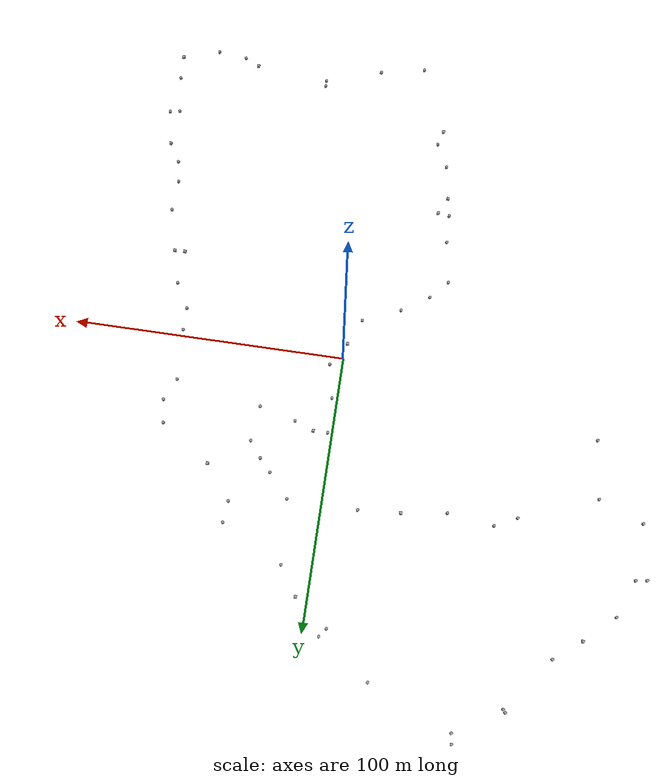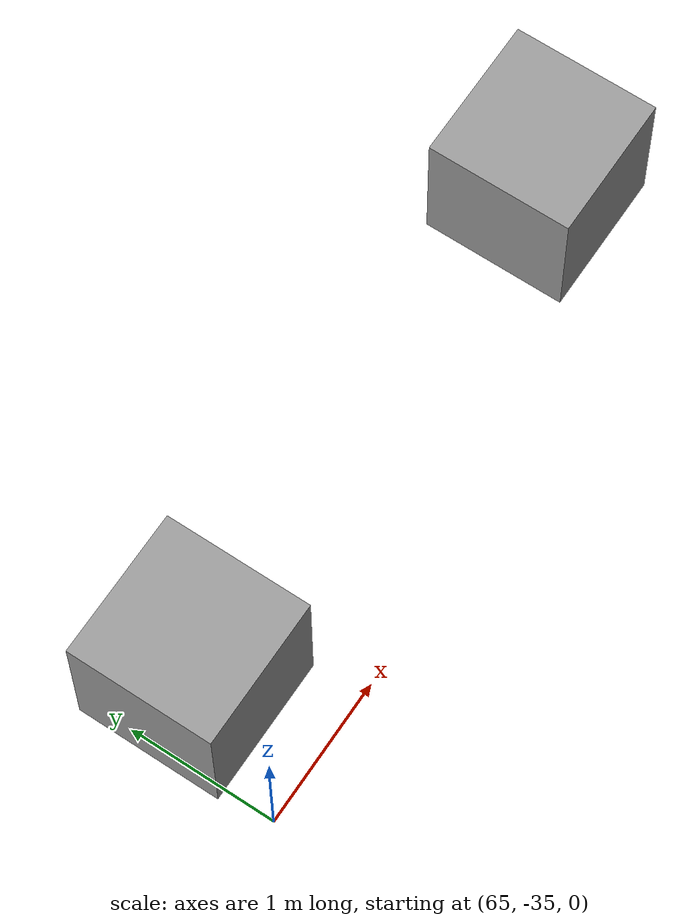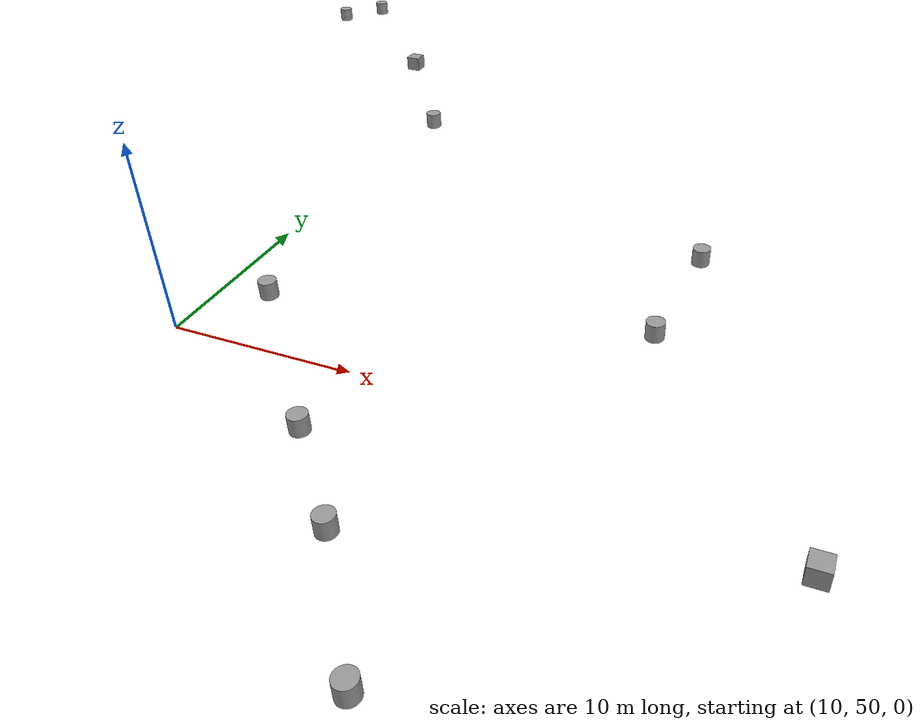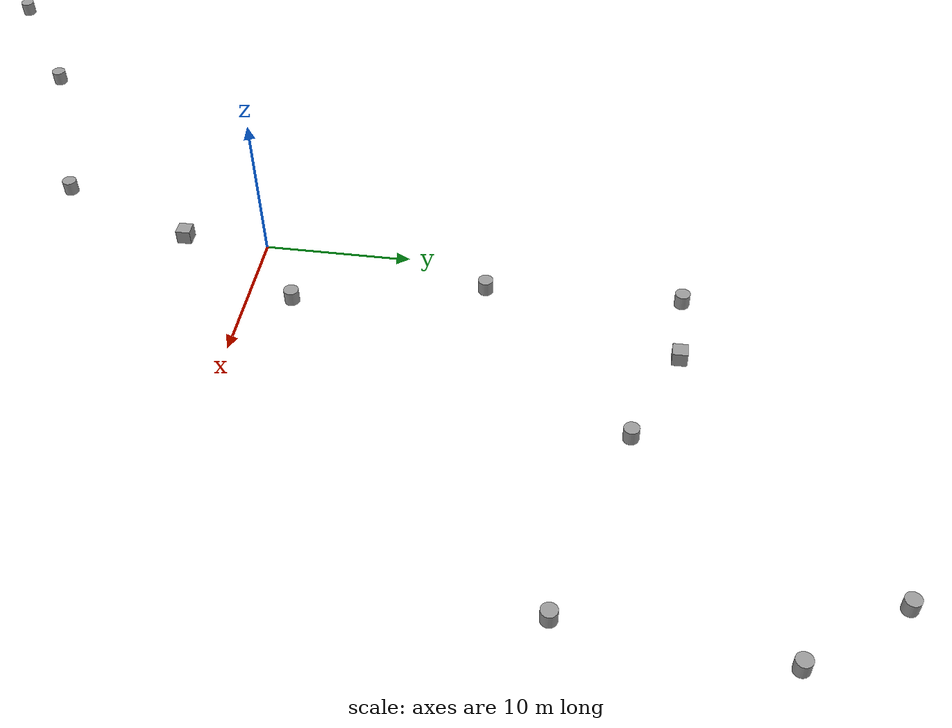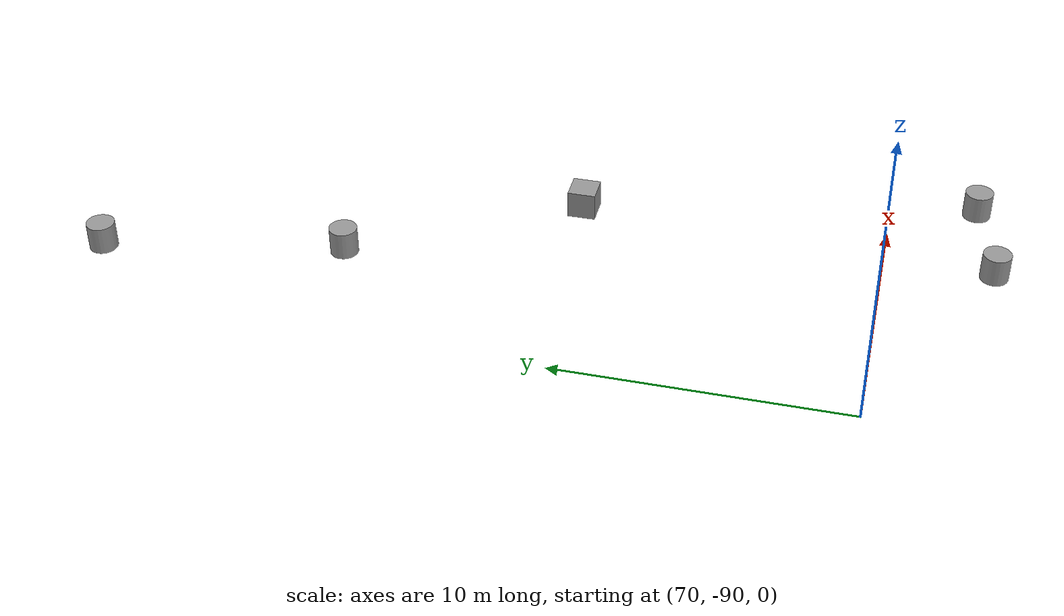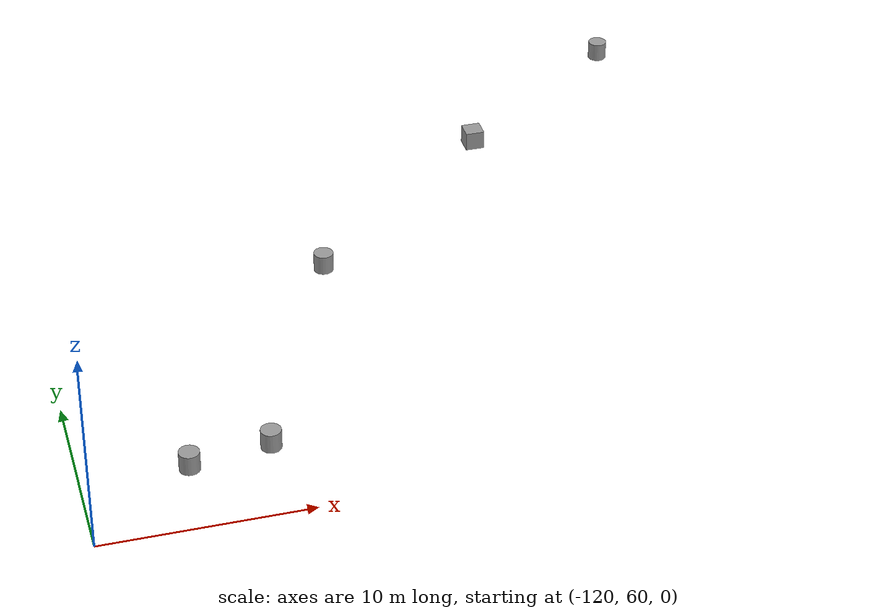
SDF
<?xml version='1.0'?>
<sdf version='1.7'>
  <model name='obstaculos'>
    <link name='link_2'>
      <inertial>
        <mass>1</mass>
        <inertia>
          <ixx>0.145833</ixx>
          <ixy>0</ixy>
          <ixz>0</ixz>
          <iyy>0.145833</iyy>
          <iyz>0</iyz>
          <izz>0.125</izz>
        </inertia>
      </inertial>
      <pose>-68.8345 49.6018 0 0 -0 0</pose>
      <visual name='visual'>
        <pose>0 0 0 0 -0 0</pose>
        <geometry>
          <cylinder>
            <radius>0.5</radius>
            <length>1</length>
          </cylinder>
        </geometry>
        <material>
          <lighting>1</lighting>
          <script>
            <uri>file://media/materials/scripts/gazebo.material</uri>
            <name>Gazebo/Grey</name>
          </script>
          <shader type='pixel'/>
        </material>
        <transparency>0</transparency>
        <cast_shadows>1</cast_shadows>
      </visual>
      <collision name='collision'>
        <laser_retro>0</laser_retro>
        <max_contacts>10</max_contacts>
        <pose>0 0 0 0 -0 0</pose>
        <geometry>
          <cylinder>
            <radius>0.5</radius>
            <length>1</length>
          </cylinder>
        </geometry>
        <surface>
          <friction>
            <ode>
              <mu>1</mu>
              <mu2>1</mu2>
              <fdir1>0 0 0</fdir1>
              <slip1>0</slip1>
              <slip2>0</slip2>
            </ode>
            <torsional>
              <coefficient>1</coefficient>
              <patch_radius>0</patch_radius>
              <surface_radius>0</surface_radius>
              <use_patch_radius>1</use_patch_radius>
              <ode>
                <slip>0</slip>
              </ode>
            </torsional>
          </friction>
          <bounce>
            <restitution_coefficient>0</restitution_coefficient>
            <threshold>1e+06</threshold>
          </bounce>
          <contact>
            <collide_without_contact>0</collide_without_contact>
            <collide_without_contact_bitmask>1</collide_without_contact_bitmask>
            <collide_bitmask>1</collide_bitmask>
            <ode>
              <soft_cfm>0</soft_cfm>
              <soft_erp>0.2</soft_erp>
              <kp>1e+13</kp>
              <kd>1</kd>
              <max_vel>0.01</max_vel>
              <min_depth>0</min_depth>
            </ode>
            <bullet>
              <split_impulse>1</split_impulse>
              <split_impulse_penetration_threshold>-0.01</split_impulse_penetration_threshold>
              <soft_cfm>0</soft_cfm>
              <soft_erp>0.2</soft_erp>
              <kp>1e+13</kp>
              <kd>1</kd>
            </bullet>
          </contact>
        </surface>
      </collision>
    </link>
    <link name='link_10'>
      <inertial>
        <mass>1</mass>
        <inertia>
          <ixx>0.145833</ixx>
          <ixy>0</ixy>
          <ixz>0</ixz>
          <iyy>0.145833</iyy>
          <iyz>0</iyz>
          <izz>0.125</izz>
        </inertia>
      </inertial>
      <pose>23.917 41.4838 0 0 -0 0</pose>
      <visual name='visual'>
        <pose>0 0 0 0 -0 0</pose>
        <geometry>
          <cylinder>
            <radius>0.5</radius>
            <length>1</length>
          </cylinder>
        </geometry>
        <material>
          <lighting>1</lighting>
          <script>
            <uri>file://media/materials/scripts/gazebo.material</uri>
            <name>Gazebo/Grey</name>
          </script>
          <shader type='pixel'/>
        </material>
        <transparency>0</transparency>
        <cast_shadows>1</cast_shadows>
      </visual>
      <collision name='collision'>
        <laser_retro>0</laser_retro>
        <max_contacts>10</max_contacts>
        <pose>0 0 0 0 -0 0</pose>
        <geometry>
          <cylinder>
            <radius>0.5</radius>
            <length>1</length>
          </cylinder>
        </geometry>
        <surface>
          <friction>
            <ode>
              <mu>1</mu>
              <mu2>1</mu2>
              <fdir1>0 0 0</fdir1>
              <slip1>0</slip1>
              <slip2>0</slip2>
            </ode>
            <torsional>
              <coefficient>1</coefficient>
              <patch_radius>0</patch_radius>
              <surface_radius>0</surface_radius>
              <use_patch_radius>1</use_patch_radius>
              <ode>
                <slip>0</slip>
              </ode>
            </torsional>
          </friction>
          <bounce>
            <restitution_coefficient>0</restitution_coefficient>
            <threshold>1e+06</threshold>
          </bounce>
          <contact>
            <collide_without_contact>0</collide_without_contact>
            <collide_without_contact_bitmask>1</collide_without_contact_bitmask>
            <collide_bitmask>1</collide_bitmask>
            <ode>
              <soft_cfm>0</soft_cfm>
              <soft_erp>0.2</soft_erp>
              <kp>1e+13</kp>
              <kd>1</kd>
              <max_vel>0.01</max_vel>
              <min_depth>0</min_depth>
            </ode>
            <bullet>
              <split_impulse>1</split_impulse>
              <split_impulse_penetration_threshold>-0.01</split_impulse_penetration_threshold>
              <soft_cfm>0</soft_cfm>
              <soft_erp>0.2</soft_erp>
              <kp>1e+13</kp>
              <kd>1</kd>
            </bullet>
          </contact>
        </surface>
      </collision>
    </link>
    <link name='link_11'>
      <inertial>
        <mass>1</mass>
        <inertia>
          <ixx>0.145833</ixx>
          <ixy>0</ixy>
          <ixz>0</ixz>
          <iyy>0.145833</iyy>
          <iyz>0</iyz>
          <izz>0.125</izz>
        </inertia>
      </inertial>
      <pose>27.1261 22.4083 0 0 -0 0</pose>
      <visual name='visual'>
        <pose>0 0 0 0 -0 0</pose>
        <geometry>
          <cylinder>
            <radius>0.5</radius>
            <length>1</length>
          </cylinder>
        </geometry>
        <material>
          <lighting>1</lighting>
          <script>
            <uri>file://media/materials/scripts/gazebo.material</uri>
            <name>Gazebo/Grey</name>
          </script>
          <shader type='pixel'/>
        </material>
        <transparency>0</transparency>
        <cast_shadows>1</cast_shadows>
      </visual>
      <collision name='collision'>
        <laser_retro>0</laser_retro>
        <max_contacts>10</max_contacts>
        <pose>0 0 0 0 -0 0</pose>
        <geometry>
          <cylinder>
            <radius>0.5</radius>
            <length>1</length>
          </cylinder>
        </geometry>
        <surface>
          <friction>
            <ode>
              <mu>1</mu>
              <mu2>1</mu2>
              <fdir1>0 0 0</fdir1>
              <slip1>0</slip1>
              <slip2>0</slip2>
            </ode>
            <torsional>
              <coefficient>1</coefficient>
              <patch_radius>0</patch_radius>
              <surface_radius>0</surface_radius>
              <use_patch_radius>1</use_patch_radius>
              <ode>
                <slip>0</slip>
              </ode>
            </torsional>
          </friction>
          <bounce>
            <restitution_coefficient>0</restitution_coefficient>
            <threshold>1e+06</threshold>
          </bounce>
          <contact>
            <collide_without_contact>0</collide_without_contact>
            <collide_without_contact_bitmask>1</collide_without_contact_bitmask>
            <collide_bitmask>1</collide_bitmask>
            <ode>
              <soft_cfm>0</soft_cfm>
              <soft_erp>0.2</soft_erp>
              <kp>1e+13</kp>
              <kd>1</kd>
              <max_vel>0.01</max_vel>
              <min_depth>0</min_depth>
            </ode>
            <bullet>
              <split_impulse>1</split_impulse>
              <split_impulse_penetration_threshold>-0.01</split_impulse_penetration_threshold>
              <soft_cfm>0</soft_cfm>
              <soft_erp>0.2</soft_erp>
              <kp>1e+13</kp>
              <kd>1</kd>
            </bullet>
          </contact>
        </surface>
      </collision>
    </link>
    <link name='link_12'>
      <inertial>
        <mass>1</mass>
        <inertia>
          <ixx>0.145833</ixx>
          <ixy>0</ixy>
          <ixz>0</ixz>
          <iyy>0.145833</iyy>
          <iyz>0</iyz>
          <izz>0.125</izz>
        </inertia>
      </inertial>
      <pose>13.8228 25.9981 0 0 -0 0</pose>
      <visual name='visual'>
        <pose>0 0 0 0 -0 0</pose>
        <geometry>
          <cylinder>
            <radius>0.5</radius>
            <length>1</length>
          </cylinder>
        </geometry>
        <material>
          <lighting>1</lighting>
          <script>
            <uri>file://media/materials/scripts/gazebo.material</uri>
            <name>Gazebo/Grey</name>
          </script>
          <shader type='pixel'/>
        </material>
        <transparency>0</transparency>
        <cast_shadows>1</cast_shadows>
      </visual>
      <collision name='collision'>
        <laser_retro>0</laser_retro>
        <max_contacts>10</max_contacts>
        <pose>0 0 0 0 -0 0</pose>
        <geometry>
          <cylinder>
            <radius>0.5</radius>
            <length>1</length>
          </cylinder>
        </geometry>
        <surface>
          <friction>
            <ode>
              <mu>1</mu>
              <mu2>1</mu2>
              <fdir1>0 0 0</fdir1>
              <slip1>0</slip1>
              <slip2>0</slip2>
            </ode>
            <torsional>
              <coefficient>1</coefficient>
              <patch_radius>0</patch_radius>
              <surface_radius>0</surface_radius>
              <use_patch_radius>1</use_patch_radius>
              <ode>
                <slip>0</slip>
              </ode>
            </torsional>
          </friction>
          <bounce>
            <restitution_coefficient>0</restitution_coefficient>
            <threshold>1e+06</threshold>
          </bounce>
          <contact>
            <collide_without_contact>0</collide_without_contact>
            <collide_without_contact_bitmask>1</collide_without_contact_bitmask>
            <collide_bitmask>1</collide_bitmask>
            <ode>
              <soft_cfm>0</soft_cfm>
              <soft_erp>0.2</soft_erp>
              <kp>1e+13</kp>
              <kd>1</kd>
              <max_vel>0.01</max_vel>
              <min_depth>0</min_depth>
            </ode>
            <bullet>
              <split_impulse>1</split_impulse>
              <split_impulse_penetration_threshold>-0.01</split_impulse_penetration_threshold>
              <soft_cfm>0</soft_cfm>
              <soft_erp>0.2</soft_erp>
              <kp>1e+13</kp>
              <kd>1</kd>
            </bullet>
          </contact>
        </surface>
      </collision>
    </link>
    <link name='link_13'>
      <inertial>
        <mass>1</mass>
        <inertia>
          <ixx>0.166667</ixx>
          <ixy>0</ixy>
          <ixz>0</ixz>
          <iyy>0.166667</iyy>
          <iyz>0</iyz>
          <izz>0.166667</izz>
        </inertia>
      </inertial>
      <pose>6.80401 28.6836 0 0 -0 0</pose>
      <visual name='visual'>
        <pose>0 0 0 0 -0 0</pose>
        <geometry>
          <box>
            <size>1 1 1</size>
          </box>
        </geometry>
        <material>
          <lighting>1</lighting>
          <script>
            <uri>file://media/materials/scripts/gazebo.material</uri>
            <name>Gazebo/Grey</name>
          </script>
          <shader type='pixel'/>
        </material>
        <transparency>0</transparency>
        <cast_shadows>1</cast_shadows>
      </visual>
      <collision name='collision'>
        <laser_retro>0</laser_retro>
        <max_contacts>10</max_contacts>
        <pose>0 0 0 0 -0 0</pose>
        <geometry>
          <box>
            <size>1 1 1</size>
          </box>
        </geometry>
        <surface>
          <friction>
            <ode>
              <mu>1</mu>
              <mu2>1</mu2>
              <fdir1>0 0 0</fdir1>
              <slip1>0</slip1>
              <slip2>0</slip2>
            </ode>
            <torsional>
              <coefficient>1</coefficient>
              <patch_radius>0</patch_radius>
              <surface_radius>0</surface_radius>
              <use_patch_radius>1</use_patch_radius>
              <ode>
                <slip>0</slip>
              </ode>
            </torsional>
          </friction>
          <bounce>
            <restitution_coefficient>0</restitution_coefficient>
            <threshold>1e+06</threshold>
          </bounce>
          <contact>
            <collide_without_contact>0</collide_without_contact>
            <collide_without_contact_bitmask>1</collide_without_contact_bitmask>
            <collide_bitmask>1</collide_bitmask>
            <ode>
              <soft_cfm>0</soft_cfm>
              <soft_erp>0.2</soft_erp>
              <kp>1e+13</kp>
              <kd>1</kd>
              <max_vel>0.01</max_vel>
              <min_depth>0</min_depth>
            </ode>
            <bullet>
              <split_impulse>1</split_impulse>
              <split_impulse_penetration_threshold>-0.01</split_impulse_penetration_threshold>
              <soft_cfm>0</soft_cfm>
              <soft_erp>0.2</soft_erp>
              <kp>1e+13</kp>
              <kd>1</kd>
            </bullet>
          </contact>
        </surface>
      </collision>
    </link>
    <link name='link_14'>
      <inertial>
        <mass>1</mass>
        <inertia>
          <ixx>0.145833</ixx>
          <ixy>0</ixy>
          <ixz>0</ixz>
          <iyy>0.145833</iyy>
          <iyz>0</iyz>
          <izz>0.125</izz>
        </inertia>
      </inertial>
      <pose>1.91987 15.5386 0 0 -0 0</pose>
      <visual name='visual'>
        <pose>0 0 0 0 -0 0</pose>
        <geometry>
          <cylinder>
            <radius>0.5</radius>
            <length>1</length>
          </cylinder>
        </geometry>
        <material>
          <lighting>1</lighting>
          <script>
            <uri>file://media/materials/scripts/gazebo.material</uri>
            <name>Gazebo/Grey</name>
          </script>
          <shader type='pixel'/>
        </material>
        <transparency>0</transparency>
        <cast_shadows>1</cast_shadows>
      </visual>
      <collision name='collision'>
        <laser_retro>0</laser_retro>
        <max_contacts>10</max_contacts>
        <pose>0 0 0 0 -0 0</pose>
        <geometry>
          <cylinder>
            <radius>0.5</radius>
            <length>1</length>
          </cylinder>
        </geometry>
        <surface>
          <friction>
            <ode>
              <mu>1</mu>
              <mu2>1</mu2>
              <fdir1>0 0 0</fdir1>
              <slip1>0</slip1>
              <slip2>0</slip2>
            </ode>
            <torsional>
              <coefficient>1</coefficient>
              <patch_radius>0</patch_radius>
              <surface_radius>0</surface_radius>
              <use_patch_radius>1</use_patch_radius>
              <ode>
                <slip>0</slip>
              </ode>
            </torsional>
          </friction>
          <bounce>
            <restitution_coefficient>0</restitution_coefficient>
            <threshold>1e+06</threshold>
          </bounce>
          <contact>
            <collide_without_contact>0</collide_without_contact>
            <collide_without_contact_bitmask>1</collide_without_contact_bitmask>
            <collide_bitmask>1</collide_bitmask>
            <ode>
              <soft_cfm>0</soft_cfm>
              <soft_erp>0.2</soft_erp>
              <kp>1e+13</kp>
              <kd>1</kd>
              <max_vel>0.01</max_vel>
              <min_depth>0</min_depth>
            </ode>
            <bullet>
              <split_impulse>1</split_impulse>
              <split_impulse_penetration_threshold>-0.01</split_impulse_penetration_threshold>
              <soft_cfm>0</soft_cfm>
              <soft_erp>0.2</soft_erp>
              <kp>1e+13</kp>
              <kd>1</kd>
            </bullet>
          </contact>
        </surface>
      </collision>
    </link>
    <link name='link_15'>
      <inertial>
        <mass>1</mass>
        <inertia>
          <ixx>0.145833</ixx>
          <ixy>0</ixy>
          <ixz>0</ixz>
          <iyy>0.145833</iyy>
          <iyz>0</iyz>
          <izz>0.125</izz>
        </inertia>
      </inertial>
      <pose>4.60069 2.83892 0 0 -0 0</pose>
      <visual name='visual'>
        <pose>0 0 0 0 -0 0</pose>
        <geometry>
          <cylinder>
            <radius>0.5</radius>
            <length>1</length>
          </cylinder>
        </geometry>
        <material>
          <lighting>1</lighting>
          <script>
            <uri>file://media/materials/scripts/gazebo.material</uri>
            <name>Gazebo/Grey</name>
          </script>
          <shader type='pixel'/>
        </material>
        <transparency>0</transparency>
        <cast_shadows>1</cast_shadows>
      </visual>
      <collision name='collision'>
        <laser_retro>0</laser_retro>
        <max_contacts>10</max_contacts>
        <pose>0 0 0 0 -0 0</pose>
        <geometry>
          <cylinder>
            <radius>0.5</radius>
            <length>1</length>
          </cylinder>
        </geometry>
        <surface>
          <friction>
            <ode>
              <mu>1</mu>
              <mu2>1</mu2>
              <fdir1>0 0 0</fdir1>
              <slip1>0</slip1>
              <slip2>0</slip2>
            </ode>
            <torsional>
              <coefficient>1</coefficient>
              <patch_radius>0</patch_radius>
              <surface_radius>0</surface_radius>
              <use_patch_radius>1</use_patch_radius>
              <ode>
                <slip>0</slip>
              </ode>
            </torsional>
          </friction>
          <bounce>
            <restitution_coefficient>0</restitution_coefficient>
            <threshold>1e+06</threshold>
          </bounce>
          <contact>
            <collide_without_contact>0</collide_without_contact>
            <collide_without_contact_bitmask>1</collide_without_contact_bitmask>
            <collide_bitmask>1</collide_bitmask>
            <ode>
              <soft_cfm>0</soft_cfm>
              <soft_erp>0.2</soft_erp>
              <kp>1e+13</kp>
              <kd>1</kd>
              <max_vel>0.01</max_vel>
              <min_depth>0</min_depth>
            </ode>
            <bullet>
              <split_impulse>1</split_impulse>
              <split_impulse_penetration_threshold>-0.01</split_impulse_penetration_threshold>
              <soft_cfm>0</soft_cfm>
              <soft_erp>0.2</soft_erp>
              <kp>1e+13</kp>
              <kd>1</kd>
            </bullet>
          </contact>
        </surface>
      </collision>
    </link>
    <link name='link_16'>
      <inertial>
        <mass>1</mass>
        <inertia>
          <ixx>0.145833</ixx>
          <ixy>0</ixy>
          <ixz>0</ixz>
          <iyy>0.145833</iyy>
          <iyz>0</iyz>
          <izz>0.125</izz>
        </inertia>
      </inertial>
      <pose>1.55298 28.6763 0 0 -0 0</pose>
      <visual name='visual'>
        <pose>0 0 0 0 -0 0</pose>
        <geometry>
          <cylinder>
            <radius>0.5</radius>
            <length>1</length>
          </cylinder>
        </geometry>
        <material>
          <lighting>1</lighting>
          <script>
            <uri>file://media/materials/scripts/gazebo.material</uri>
            <name>Gazebo/Grey</name>
          </script>
          <shader type='pixel'/>
        </material>
        <transparency>0</transparency>
        <cast_shadows>1</cast_shadows>
      </visual>
      <collision name='collision'>
        <laser_retro>0</laser_retro>
        <max_contacts>10</max_contacts>
        <pose>0 0 0 0 -0 0</pose>
        <geometry>
          <cylinder>
            <radius>0.5</radius>
            <length>1</length>
          </cylinder>
        </geometry>
        <surface>
          <friction>
            <ode>
              <mu>1</mu>
              <mu2>1</mu2>
              <fdir1>0 0 0</fdir1>
              <slip1>0</slip1>
              <slip2>0</slip2>
            </ode>
            <torsional>
              <coefficient>1</coefficient>
              <patch_radius>0</patch_radius>
              <surface_radius>0</surface_radius>
              <use_patch_radius>1</use_patch_radius>
              <ode>
                <slip>0</slip>
              </ode>
            </torsional>
          </friction>
          <bounce>
            <restitution_coefficient>0</restitution_coefficient>
            <threshold>1e+06</threshold>
          </bounce>
          <contact>
            <collide_without_contact>0</collide_without_contact>
            <collide_without_contact_bitmask>1</collide_without_contact_bitmask>
            <collide_bitmask>1</collide_bitmask>
            <ode>
              <soft_cfm>0</soft_cfm>
              <soft_erp>0.2</soft_erp>
              <kp>1e+13</kp>
              <kd>1</kd>
              <max_vel>0.01</max_vel>
              <min_depth>0</min_depth>
            </ode>
            <bullet>
              <split_impulse>1</split_impulse>
              <split_impulse_penetration_threshold>-0.01</split_impulse_penetration_threshold>
              <soft_cfm>0</soft_cfm>
              <soft_erp>0.2</soft_erp>
              <kp>1e+13</kp>
              <kd>1</kd>
            </bullet>
          </contact>
        </surface>
      </collision>
    </link>
    <link name='link_17'>
      <inertial>
        <mass>1</mass>
        <inertia>
          <ixx>0.145833</ixx>
          <ixy>0</ixy>
          <ixz>0</ixz>
          <iyy>0.145833</iyy>
          <iyz>0</iyz>
          <izz>0.125</izz>
        </inertia>
      </inertial>
      <pose>-4.79054 -16.0996 0 0 -0 0</pose>
      <visual name='visual'>
        <pose>0 0 0 0 -0 0</pose>
        <geometry>
          <cylinder>
            <radius>0.5</radius>
            <length>1</length>
          </cylinder>
        </geometry>
        <material>
          <lighting>1</lighting>
          <script>
            <uri>file://media/materials/scripts/gazebo.material</uri>
            <name>Gazebo/Grey</name>
          </script>
          <shader type='pixel'/>
        </material>
        <transparency>0</transparency>
        <cast_shadows>1</cast_shadows>
      </visual>
      <collision name='collision'>
        <laser_retro>0</laser_retro>
        <max_contacts>10</max_contacts>
        <pose>0 0 0 0 -0 0</pose>
        <geometry>
          <cylinder>
            <radius>0.5</radius>
            <length>1</length>
          </cylinder>
        </geometry>
        <surface>
          <friction>
            <ode>
              <mu>1</mu>
              <mu2>1</mu2>
              <fdir1>0 0 0</fdir1>
              <slip1>0</slip1>
              <slip2>0</slip2>
            </ode>
            <torsional>
              <coefficient>1</coefficient>
              <patch_radius>0</patch_radius>
              <surface_radius>0</surface_radius>
              <use_patch_radius>1</use_patch_radius>
              <ode>
                <slip>0</slip>
              </ode>
            </torsional>
          </friction>
          <bounce>
            <restitution_coefficient>0</restitution_coefficient>
            <threshold>1e+06</threshold>
          </bounce>
          <contact>
            <collide_without_contact>0</collide_without_contact>
            <collide_without_contact_bitmask>1</collide_without_contact_bitmask>
            <collide_bitmask>1</collide_bitmask>
            <ode>
              <soft_cfm>0</soft_cfm>
              <soft_erp>0.2</soft_erp>
              <kp>1e+13</kp>
              <kd>1</kd>
              <max_vel>0.01</max_vel>
              <min_depth>0</min_depth>
            </ode>
            <bullet>
              <split_impulse>1</split_impulse>
              <split_impulse_penetration_threshold>-0.01</split_impulse_penetration_threshold>
              <soft_cfm>0</soft_cfm>
              <soft_erp>0.2</soft_erp>
              <kp>1e+13</kp>
              <kd>1</kd>
            </bullet>
          </contact>
        </surface>
      </collision>
    </link>
    <link name='link_18'>
      <inertial>
        <mass>1</mass>
        <inertia>
          <ixx>0.166667</ixx>
          <ixy>0</ixy>
          <ixz>0</ixz>
          <iyy>0.166667</iyy>
          <iyz>0</iyz>
          <izz>0.166667</izz>
        </inertia>
      </inertial>
      <pose>-0.666415 -6.12016 0 0 -0 0</pose>
      <visual name='visual'>
        <pose>0 0 0 0 -0 0</pose>
        <geometry>
          <box>
            <size>1 1 1</size>
          </box>
        </geometry>
        <material>
          <lighting>1</lighting>
          <script>
            <uri>file://media/materials/scripts/gazebo.material</uri>
            <name>Gazebo/Grey</name>
          </script>
          <shader type='pixel'/>
        </material>
        <transparency>0</transparency>
        <cast_shadows>1</cast_shadows>
      </visual>
      <collision name='collision'>
        <laser_retro>0</laser_retro>
        <max_contacts>10</max_contacts>
        <pose>0 0 0 0 -0 0</pose>
        <geometry>
          <box>
            <size>1 1 1</size>
          </box>
        </geometry>
        <surface>
          <friction>
            <ode>
              <mu>1</mu>
              <mu2>1</mu2>
              <fdir1>0 0 0</fdir1>
              <slip1>0</slip1>
              <slip2>0</slip2>
            </ode>
            <torsional>
              <coefficient>1</coefficient>
              <patch_radius>0</patch_radius>
              <surface_radius>0</surface_radius>
              <use_patch_radius>1</use_patch_radius>
              <ode>
                <slip>0</slip>
              </ode>
            </torsional>
          </friction>
          <bounce>
            <restitution_coefficient>0</restitution_coefficient>
            <threshold>1e+06</threshold>
          </bounce>
          <contact>
            <collide_without_contact>0</collide_without_contact>
            <collide_without_contact_bitmask>1</collide_without_contact_bitmask>
            <collide_bitmask>1</collide_bitmask>
            <ode>
              <soft_cfm>0</soft_cfm>
              <soft_erp>0.2</soft_erp>
              <kp>1e+13</kp>
              <kd>1</kd>
              <max_vel>0.01</max_vel>
              <min_depth>0</min_depth>
            </ode>
            <bullet>
              <split_impulse>1</split_impulse>
              <split_impulse_penetration_threshold>-0.01</split_impulse_penetration_threshold>
              <soft_cfm>0</soft_cfm>
              <soft_erp>0.2</soft_erp>
              <kp>1e+13</kp>
              <kd>1</kd>
            </bullet>
          </contact>
        </surface>
      </collision>
    </link>
    <link name='link_19'>
      <inertial>
        <mass>1</mass>
        <inertia>
          <ixx>0.145833</ixx>
          <ixy>0</ixy>
          <ixz>0</ixz>
          <iyy>0.145833</iyy>
          <iyz>0</iyz>
          <izz>0.125</izz>
        </inertia>
      </inertial>
      <pose>-18.5164 -22.2528 0 0 -0 0</pose>
      <visual name='visual'>
        <pose>0 0 0 0 -0 0</pose>
        <geometry>
          <cylinder>
            <radius>0.5</radius>
            <length>1</length>
          </cylinder>
        </geometry>
        <material>
          <lighting>1</lighting>
          <script>
            <uri>file://media/materials/scripts/gazebo.material</uri>
            <name>Gazebo/Grey</name>
          </script>
          <shader type='pixel'/>
        </material>
        <transparency>0</transparency>
        <cast_shadows>1</cast_shadows>
      </visual>
      <collision name='collision'>
        <laser_retro>0</laser_retro>
        <max_contacts>10</max_contacts>
        <pose>0 0 0 0 -0 0</pose>
        <geometry>
          <cylinder>
            <radius>0.5</radius>
            <length>1</length>
          </cylinder>
        </geometry>
        <surface>
          <friction>
            <ode>
              <mu>1</mu>
              <mu2>1</mu2>
              <fdir1>0 0 0</fdir1>
              <slip1>0</slip1>
              <slip2>0</slip2>
            </ode>
            <torsional>
              <coefficient>1</coefficient>
              <patch_radius>0</patch_radius>
              <surface_radius>0</surface_radius>
              <use_patch_radius>1</use_patch_radius>
              <ode>
                <slip>0</slip>
              </ode>
            </torsional>
          </friction>
          <bounce>
            <restitution_coefficient>0</restitution_coefficient>
            <threshold>1e+06</threshold>
          </bounce>
          <contact>
            <collide_without_contact>0</collide_without_contact>
            <collide_without_contact_bitmask>1</collide_without_contact_bitmask>
            <collide_bitmask>1</collide_bitmask>
            <ode>
              <soft_cfm>0</soft_cfm>
              <soft_erp>0.2</soft_erp>
              <kp>1e+13</kp>
              <kd>1</kd>
              <max_vel>0.01</max_vel>
              <min_depth>0</min_depth>
            </ode>
            <bullet>
              <split_impulse>1</split_impulse>
              <split_impulse_penetration_threshold>-0.01</split_impulse_penetration_threshold>
              <soft_cfm>0</soft_cfm>
              <soft_erp>0.2</soft_erp>
              <kp>1e+13</kp>
              <kd>1</kd>
            </bullet>
          </contact>
        </surface>
      </collision>
    </link>
    <link name='link_20'>
      <inertial>
        <mass>1</mass>
        <inertia>
          <ixx>0.145833</ixx>
          <ixy>0</ixy>
          <ixz>0</ixz>
          <iyy>0.145833</iyy>
          <iyz>0</iyz>
          <izz>0.125</izz>
        </inertia>
      </inertial>
      <pose>-28.5098 -28.9625 0 0 -0 0</pose>
      <visual name='visual'>
        <pose>0 0 0 0 -0 0</pose>
        <geometry>
          <cylinder>
            <radius>0.5</radius>
            <length>1</length>
          </cylinder>
        </geometry>
        <material>
          <lighting>1</lighting>
          <script>
            <uri>file://media/materials/scripts/gazebo.material</uri>
            <name>Gazebo/Grey</name>
          </script>
          <shader type='pixel'/>
        </material>
        <transparency>0</transparency>
        <cast_shadows>1</cast_shadows>
      </visual>
      <collision name='collision'>
        <laser_retro>0</laser_retro>
        <max_contacts>10</max_contacts>
        <pose>0 0 0 0 -0 0</pose>
        <geometry>
          <cylinder>
            <radius>0.5</radius>
            <length>1</length>
          </cylinder>
        </geometry>
        <surface>
          <friction>
            <ode>
              <mu>1</mu>
              <mu2>1</mu2>
              <fdir1>0 0 0</fdir1>
              <slip1>0</slip1>
              <slip2>0</slip2>
            </ode>
            <torsional>
              <coefficient>1</coefficient>
              <patch_radius>0</patch_radius>
              <surface_radius>0</surface_radius>
              <use_patch_radius>1</use_patch_radius>
              <ode>
                <slip>0</slip>
              </ode>
            </torsional>
          </friction>
          <bounce>
            <restitution_coefficient>0</restitution_coefficient>
            <threshold>1e+06</threshold>
          </bounce>
          <contact>
            <collide_without_contact>0</collide_without_contact>
            <collide_without_contact_bitmask>1</collide_without_contact_bitmask>
            <collide_bitmask>1</collide_bitmask>
            <ode>
              <soft_cfm>0</soft_cfm>
              <soft_erp>0.2</soft_erp>
              <kp>1e+13</kp>
              <kd>1</kd>
              <max_vel>0.01</max_vel>
              <min_depth>0</min_depth>
            </ode>
            <bullet>
              <split_impulse>1</split_impulse>
              <split_impulse_penetration_threshold>-0.01</split_impulse_penetration_threshold>
              <soft_cfm>0</soft_cfm>
              <soft_erp>0.2</soft_erp>
              <kp>1e+13</kp>
              <kd>1</kd>
            </bullet>
          </contact>
        </surface>
      </collision>
    </link>
    <link name='link_21'>
      <inertial>
        <mass>1</mass>
        <inertia>
          <ixx>0.145833</ixx>
          <ixy>0</ixy>
          <ixz>0</ixz>
          <iyy>0.145833</iyy>
          <iyz>0</iyz>
          <izz>0.125</izz>
        </inertia>
      </inertial>
      <pose>-34.6644 -35.9676 0 0 -0 0</pose>
      <visual name='visual'>
        <pose>0 0 0 0 -0 0</pose>
        <geometry>
          <cylinder>
            <radius>0.5</radius>
            <length>1</length>
          </cylinder>
        </geometry>
        <material>
          <lighting>1</lighting>
          <script>
            <uri>file://media/materials/scripts/gazebo.material</uri>
            <name>Gazebo/Grey</name>
          </script>
          <shader type='pixel'/>
        </material>
        <transparency>0</transparency>
        <cast_shadows>1</cast_shadows>
      </visual>
      <collision name='collision'>
        <laser_retro>0</laser_retro>
        <max_contacts>10</max_contacts>
        <pose>0 0 0 0 -0 0</pose>
        <geometry>
          <cylinder>
            <radius>0.5</radius>
            <length>1</length>
          </cylinder>
        </geometry>
        <surface>
          <friction>
            <ode>
              <mu>1</mu>
              <mu2>1</mu2>
              <fdir1>0 0 0</fdir1>
              <slip1>0</slip1>
              <slip2>0</slip2>
            </ode>
            <torsional>
              <coefficient>1</coefficient>
              <patch_radius>0</patch_radius>
              <surface_radius>0</surface_radius>
              <use_patch_radius>1</use_patch_radius>
              <ode>
                <slip>0</slip>
              </ode>
            </torsional>
          </friction>
          <bounce>
            <restitution_coefficient>0</restitution_coefficient>
            <threshold>1e+06</threshold>
          </bounce>
          <contact>
            <collide_without_contact>0</collide_without_contact>
            <collide_without_contact_bitmask>1</collide_without_contact_bitmask>
            <collide_bitmask>1</collide_bitmask>
            <ode>
              <soft_cfm>0</soft_cfm>
              <soft_erp>0.2</soft_erp>
              <kp>1e+13</kp>
              <kd>1</kd>
              <max_vel>0.01</max_vel>
              <min_depth>0</min_depth>
            </ode>
            <bullet>
              <split_impulse>1</split_impulse>
              <split_impulse_penetration_threshold>-0.01</split_impulse_penetration_threshold>
              <soft_cfm>0</soft_cfm>
              <soft_erp>0.2</soft_erp>
              <kp>1e+13</kp>
              <kd>1</kd>
            </bullet>
          </contact>
        </surface>
      </collision>
    </link>
    <link name='link_22'>
      <inertial>
        <mass>1</mass>
        <inertia>
          <ixx>0.145833</ixx>
          <ixy>0</ixy>
          <ixz>0</ixz>
          <iyy>0.145833</iyy>
          <iyz>0</iyz>
          <izz>0.125</izz>
        </inertia>
      </inertial>
      <pose>-32.1922 -52.4288 0 0 -0 0</pose>
      <visual name='visual'>
        <pose>0 0 0 0 -0 0</pose>
        <geometry>
          <cylinder>
            <radius>0.5</radius>
            <length>1</length>
          </cylinder>
        </geometry>
        <material>
          <lighting>1</lighting>
          <script>
            <uri>file://media/materials/scripts/gazebo.material</uri>
            <name>Gazebo/Grey</name>
          </script>
          <shader type='pixel'/>
        </material>
        <transparency>0</transparency>
        <cast_shadows>1</cast_shadows>
      </visual>
      <collision name='collision'>
        <laser_retro>0</laser_retro>
        <max_contacts>10</max_contacts>
        <pose>0 0 0 0 -0 0</pose>
        <geometry>
          <cylinder>
            <radius>0.5</radius>
            <length>1</length>
          </cylinder>
        </geometry>
        <surface>
          <friction>
            <ode>
              <mu>1</mu>
              <mu2>1</mu2>
              <fdir1>0 0 0</fdir1>
              <slip1>0</slip1>
              <slip2>0</slip2>
            </ode>
            <torsional>
              <coefficient>1</coefficient>
              <patch_radius>0</patch_radius>
              <surface_radius>0</surface_radius>
              <use_patch_radius>1</use_patch_radius>
              <ode>
                <slip>0</slip>
              </ode>
            </torsional>
          </friction>
          <bounce>
            <restitution_coefficient>0</restitution_coefficient>
            <threshold>1e+06</threshold>
          </bounce>
          <contact>
            <collide_without_contact>0</collide_without_contact>
            <collide_without_contact_bitmask>1</collide_without_contact_bitmask>
            <collide_bitmask>1</collide_bitmask>
            <ode>
              <soft_cfm>0</soft_cfm>
              <soft_erp>0.2</soft_erp>
              <kp>1e+13</kp>
              <kd>1</kd>
              <max_vel>0.01</max_vel>
              <min_depth>0</min_depth>
            </ode>
            <bullet>
              <split_impulse>1</split_impulse>
              <split_impulse_penetration_threshold>-0.01</split_impulse_penetration_threshold>
              <soft_cfm>0</soft_cfm>
              <soft_erp>0.2</soft_erp>
              <kp>1e+13</kp>
              <kd>1</kd>
            </bullet>
          </contact>
        </surface>
      </collision>
    </link>
    <link name='link_23'>
      <inertial>
        <mass>1</mass>
        <inertia>
          <ixx>0.166667</ixx>
          <ixy>0</ixy>
          <ixz>0</ixz>
          <iyy>0.166667</iyy>
          <iyz>0</iyz>
          <izz>0.166667</izz>
        </inertia>
      </inertial>
      <pose>-27.5481 -64.2829 0 0 -0 0</pose>
      <visual name='visual'>
        <pose>0 0 0 0 -0 0</pose>
        <geometry>
          <box>
            <size>1 1 1</size>
          </box>
        </geometry>
        <material>
          <lighting>1</lighting>
          <script>
            <uri>file://media/materials/scripts/gazebo.material</uri>
            <name>Gazebo/Grey</name>
          </script>
          <shader type='pixel'/>
        </material>
        <transparency>0</transparency>
        <cast_shadows>1</cast_shadows>
      </visual>
      <collision name='collision'>
        <laser_retro>0</laser_retro>
        <max_contacts>10</max_contacts>
        <pose>0 0 0 0 -0 0</pose>
        <geometry>
          <box>
            <size>1 1 1</size>
          </box>
        </geometry>
        <surface>
          <friction>
            <ode>
              <mu>1</mu>
              <mu2>1</mu2>
              <fdir1>0 0 0</fdir1>
              <slip1>0</slip1>
              <slip2>0</slip2>
            </ode>
            <torsional>
              <coefficient>1</coefficient>
              <patch_radius>0</patch_radius>
              <surface_radius>0</surface_radius>
              <use_patch_radius>1</use_patch_radius>
              <ode>
                <slip>0</slip>
              </ode>
            </torsional>
          </friction>
          <bounce>
            <restitution_coefficient>0</restitution_coefficient>
            <threshold>1e+06</threshold>
          </bounce>
          <contact>
            <collide_without_contact>0</collide_without_contact>
            <collide_without_contact_bitmask>1</collide_without_contact_bitmask>
            <collide_bitmask>1</collide_bitmask>
            <ode>
              <soft_cfm>0</soft_cfm>
              <soft_erp>0.2</soft_erp>
              <kp>1e+13</kp>
              <kd>1</kd>
              <max_vel>0.01</max_vel>
              <min_depth>0</min_depth>
            </ode>
            <bullet>
              <split_impulse>1</split_impulse>
              <split_impulse_penetration_threshold>-0.01</split_impulse_penetration_threshold>
              <soft_cfm>0</soft_cfm>
              <soft_erp>0.2</soft_erp>
              <kp>1e+13</kp>
              <kd>1</kd>
            </bullet>
          </contact>
        </surface>
      </collision>
    </link>
    <link name='link_24'>
      <inertial>
        <mass>1</mass>
        <inertia>
          <ixx>0.166667</ixx>
          <ixy>0</ixy>
          <ixz>0</ixz>
          <iyy>0.166667</iyy>
          <iyz>0</iyz>
          <izz>0.166667</izz>
        </inertia>
      </inertial>
      <pose>-30.5685 -70.8884 0 0 -0 0</pose>
      <visual name='visual'>
        <pose>0 0 0 0 -0 0</pose>
        <geometry>
          <box>
            <size>1 1 1</size>
          </box>
        </geometry>
        <material>
          <lighting>1</lighting>
          <script>
            <uri>file://media/materials/scripts/gazebo.material</uri>
            <name>Gazebo/Grey</name>
          </script>
          <shader type='pixel'/>
        </material>
        <transparency>0</transparency>
        <cast_shadows>1</cast_shadows>
      </visual>
      <collision name='collision'>
        <laser_retro>0</laser_retro>
        <max_contacts>10</max_contacts>
        <pose>0 0 0 0 -0 0</pose>
        <geometry>
          <box>
            <size>1 1 1</size>
          </box>
        </geometry>
        <surface>
          <friction>
            <ode>
              <mu>1</mu>
              <mu2>1</mu2>
              <fdir1>0 0 0</fdir1>
              <slip1>0</slip1>
              <slip2>0</slip2>
            </ode>
            <torsional>
              <coefficient>1</coefficient>
              <patch_radius>0</patch_radius>
              <surface_radius>0</surface_radius>
              <use_patch_radius>1</use_patch_radius>
              <ode>
                <slip>0</slip>
              </ode>
            </torsional>
          </friction>
          <bounce>
            <restitution_coefficient>0</restitution_coefficient>
            <threshold>1e+06</threshold>
          </bounce>
          <contact>
            <collide_without_contact>0</collide_without_contact>
            <collide_without_contact_bitmask>1</collide_without_contact_bitmask>
            <collide_bitmask>1</collide_bitmask>
            <ode>
              <soft_cfm>0</soft_cfm>
              <soft_erp>0.2</soft_erp>
              <kp>1e+13</kp>
              <kd>1</kd>
              <max_vel>0.01</max_vel>
              <min_depth>0</min_depth>
            </ode>
            <bullet>
              <split_impulse>1</split_impulse>
              <split_impulse_penetration_threshold>-0.01</split_impulse_penetration_threshold>
              <soft_cfm>0</soft_cfm>
              <soft_erp>0.2</soft_erp>
              <kp>1e+13</kp>
              <kd>1</kd>
            </bullet>
          </contact>
        </surface>
      </collision>
    </link>
    <link name='link_25'>
      <inertial>
        <mass>1</mass>
        <inertia>
          <ixx>0.145833</ixx>
          <ixy>0</ixy>
          <ixz>0</ixz>
          <iyy>0.145833</iyy>
          <iyz>0</iyz>
          <izz>0.125</izz>
        </inertia>
      </inertial>
      <pose>-31.8533 -63.6673 0 0 -0 0</pose>
      <visual name='visual'>
        <pose>0 0 0 0 -0 0</pose>
        <geometry>
          <cylinder>
            <radius>0.5</radius>
            <length>1</length>
          </cylinder>
        </geometry>
        <material>
          <lighting>1</lighting>
          <script>
            <uri>file://media/materials/scripts/gazebo.material</uri>
            <name>Gazebo/Grey</name>
          </script>
          <shader type='pixel'/>
        </material>
        <transparency>0</transparency>
        <cast_shadows>1</cast_shadows>
      </visual>
      <collision name='collision'>
        <laser_retro>0</laser_retro>
        <max_contacts>10</max_contacts>
        <pose>0 0 0 0 -0 0</pose>
        <geometry>
          <cylinder>
            <radius>0.5</radius>
            <length>1</length>
          </cylinder>
        </geometry>
        <surface>
          <friction>
            <ode>
              <mu>1</mu>
              <mu2>1</mu2>
              <fdir1>0 0 0</fdir1>
              <slip1>0</slip1>
              <slip2>0</slip2>
            </ode>
            <torsional>
              <coefficient>1</coefficient>
              <patch_radius>0</patch_radius>
              <surface_radius>0</surface_radius>
              <use_patch_radius>1</use_patch_radius>
              <ode>
                <slip>0</slip>
              </ode>
            </torsional>
          </friction>
          <bounce>
            <restitution_coefficient>0</restitution_coefficient>
            <threshold>1e+06</threshold>
          </bounce>
          <contact>
            <collide_without_contact>0</collide_without_contact>
            <collide_without_contact_bitmask>1</collide_without_contact_bitmask>
            <collide_bitmask>1</collide_bitmask>
            <ode>
              <soft_cfm>0</soft_cfm>
              <soft_erp>0.2</soft_erp>
              <kp>1e+13</kp>
              <kd>1</kd>
              <max_vel>0.01</max_vel>
              <min_depth>0</min_depth>
            </ode>
            <bullet>
              <split_impulse>1</split_impulse>
              <split_impulse_penetration_threshold>-0.01</split_impulse_penetration_threshold>
              <soft_cfm>0</soft_cfm>
              <soft_erp>0.2</soft_erp>
              <kp>1e+13</kp>
              <kd>1</kd>
            </bullet>
          </contact>
        </surface>
      </collision>
    </link>
    <link name='link_26'>
      <inertial>
        <mass>1</mass>
        <inertia>
          <ixx>0.145833</ixx>
          <ixy>0</ixy>
          <ixz>0</ixz>
          <iyy>0.145833</iyy>
          <iyz>0</iyz>
          <izz>0.125</izz>
        </inertia>
      </inertial>
      <pose>-28.4551 -84.4776 0 0 -0 0</pose>
      <visual name='visual'>
        <pose>0 0 0 0 -0 0</pose>
        <geometry>
          <cylinder>
            <radius>0.5</radius>
            <length>1</length>
          </cylinder>
        </geometry>
        <material>
          <lighting>1</lighting>
          <script>
            <uri>file://media/materials/scripts/gazebo.material</uri>
            <name>Gazebo/Grey</name>
          </script>
          <shader type='pixel'/>
        </material>
        <transparency>0</transparency>
        <cast_shadows>1</cast_shadows>
      </visual>
      <collision name='collision'>
        <laser_retro>0</laser_retro>
        <max_contacts>10</max_contacts>
        <pose>0 0 0 0 -0 0</pose>
        <geometry>
          <cylinder>
            <radius>0.5</radius>
            <length>1</length>
          </cylinder>
        </geometry>
        <surface>
          <friction>
            <ode>
              <mu>1</mu>
              <mu2>1</mu2>
              <fdir1>0 0 0</fdir1>
              <slip1>0</slip1>
              <slip2>0</slip2>
            </ode>
            <torsional>
              <coefficient>1</coefficient>
              <patch_radius>0</patch_radius>
              <surface_radius>0</surface_radius>
              <use_patch_radius>1</use_patch_radius>
              <ode>
                <slip>0</slip>
              </ode>
            </torsional>
          </friction>
          <bounce>
            <restitution_coefficient>0</restitution_coefficient>
            <threshold>1e+06</threshold>
          </bounce>
          <contact>
            <collide_without_contact>0</collide_without_contact>
            <collide_without_contact_bitmask>1</collide_without_contact_bitmask>
            <collide_bitmask>1</collide_bitmask>
            <ode>
              <soft_cfm>0</soft_cfm>
              <soft_erp>0.2</soft_erp>
              <kp>1e+13</kp>
              <kd>1</kd>
              <max_vel>0.01</max_vel>
              <min_depth>0</min_depth>
            </ode>
            <bullet>
              <split_impulse>1</split_impulse>
              <split_impulse_penetration_threshold>-0.01</split_impulse_penetration_threshold>
              <soft_cfm>0</soft_cfm>
              <soft_erp>0.2</soft_erp>
              <kp>1e+13</kp>
              <kd>1</kd>
            </bullet>
          </contact>
        </surface>
      </collision>
    </link>
    <link name='link_27'>
      <inertial>
        <mass>1</mass>
        <inertia>
          <ixx>0.145833</ixx>
          <ixy>0</ixy>
          <ixz>0</ixz>
          <iyy>0.145833</iyy>
          <iyz>0</iyz>
          <izz>0.125</izz>
        </inertia>
      </inertial>
      <pose>-23.9145 -93.9423 0 0 -0 0</pose>
      <visual name='visual'>
        <pose>0 0 0 0 -0 0</pose>
        <geometry>
          <cylinder>
            <radius>0.5</radius>
            <length>1</length>
          </cylinder>
        </geometry>
        <material>
          <lighting>1</lighting>
          <script>
            <uri>file://media/materials/scripts/gazebo.material</uri>
            <name>Gazebo/Grey</name>
          </script>
          <shader type='pixel'/>
        </material>
        <transparency>0</transparency>
        <cast_shadows>1</cast_shadows>
      </visual>
      <collision name='collision'>
        <laser_retro>0</laser_retro>
        <max_contacts>10</max_contacts>
        <pose>0 0 0 0 -0 0</pose>
        <geometry>
          <cylinder>
            <radius>0.5</radius>
            <length>1</length>
          </cylinder>
        </geometry>
        <surface>
          <friction>
            <ode>
              <mu>1</mu>
              <mu2>1</mu2>
              <fdir1>0 0 0</fdir1>
              <slip1>0</slip1>
              <slip2>0</slip2>
            </ode>
            <torsional>
              <coefficient>1</coefficient>
              <patch_radius>0</patch_radius>
              <surface_radius>0</surface_radius>
              <use_patch_radius>1</use_patch_radius>
              <ode>
                <slip>0</slip>
              </ode>
            </torsional>
          </friction>
          <bounce>
            <restitution_coefficient>0</restitution_coefficient>
            <threshold>1e+06</threshold>
          </bounce>
          <contact>
            <collide_without_contact>0</collide_without_contact>
            <collide_without_contact_bitmask>1</collide_without_contact_bitmask>
            <collide_bitmask>1</collide_bitmask>
            <ode>
              <soft_cfm>0</soft_cfm>
              <soft_erp>0.2</soft_erp>
              <kp>1e+13</kp>
              <kd>1</kd>
              <max_vel>0.01</max_vel>
              <min_depth>0</min_depth>
            </ode>
            <bullet>
              <split_impulse>1</split_impulse>
              <split_impulse_penetration_threshold>-0.01</split_impulse_penetration_threshold>
              <soft_cfm>0</soft_cfm>
              <soft_erp>0.2</soft_erp>
              <kp>1e+13</kp>
              <kd>1</kd>
            </bullet>
          </contact>
        </surface>
      </collision>
    </link>
    <link name='link_28'>
      <inertial>
        <mass>1</mass>
        <inertia>
          <ixx>0.166667</ixx>
          <ixy>0</ixy>
          <ixz>0</ixz>
          <iyy>0.166667</iyy>
          <iyz>0</iyz>
          <izz>0.166667</izz>
        </inertia>
      </inertial>
      <pose>-25.5345 -99.8334 0 0 -0 0</pose>
      <visual name='visual'>
        <pose>0 0 0 0 -0 0</pose>
        <geometry>
          <box>
            <size>1 1 1</size>
          </box>
        </geometry>
        <material>
          <lighting>1</lighting>
          <script>
            <uri>file://media/materials/scripts/gazebo.material</uri>
            <name>Gazebo/Grey</name>
          </script>
          <shader type='pixel'/>
        </material>
        <transparency>0</transparency>
        <cast_shadows>1</cast_shadows>
      </visual>
      <collision name='collision'>
        <laser_retro>0</laser_retro>
        <max_contacts>10</max_contacts>
        <pose>0 0 0 0 -0 0</pose>
        <geometry>
          <box>
            <size>1 1 1</size>
          </box>
        </geometry>
        <surface>
          <friction>
            <ode>
              <mu>1</mu>
              <mu2>1</mu2>
              <fdir1>0 0 0</fdir1>
              <slip1>0</slip1>
              <slip2>0</slip2>
            </ode>
            <torsional>
              <coefficient>1</coefficient>
              <patch_radius>0</patch_radius>
              <surface_radius>0</surface_radius>
              <use_patch_radius>1</use_patch_radius>
              <ode>
                <slip>0</slip>
              </ode>
            </torsional>
          </friction>
          <bounce>
            <restitution_coefficient>0</restitution_coefficient>
            <threshold>1e+06</threshold>
          </bounce>
          <contact>
            <collide_without_contact>0</collide_without_contact>
            <collide_without_contact_bitmask>1</collide_without_contact_bitmask>
            <collide_bitmask>1</collide_bitmask>
            <ode>
              <soft_cfm>0</soft_cfm>
              <soft_erp>0.2</soft_erp>
              <kp>1e+13</kp>
              <kd>1</kd>
              <max_vel>0.01</max_vel>
              <min_depth>0</min_depth>
            </ode>
            <bullet>
              <split_impulse>1</split_impulse>
              <split_impulse_penetration_threshold>-0.01</split_impulse_penetration_threshold>
              <soft_cfm>0</soft_cfm>
              <soft_erp>0.2</soft_erp>
              <kp>1e+13</kp>
              <kd>1</kd>
            </bullet>
          </contact>
        </surface>
      </collision>
    </link>
    <link name='link_29'>
      <inertial>
        <mass>1</mass>
        <inertia>
          <ixx>0.145833</ixx>
          <ixy>0</ixy>
          <ixz>0</ixz>
          <iyy>0.145833</iyy>
          <iyz>0</iyz>
          <izz>0.125</izz>
        </inertia>
      </inertial>
      <pose>-14.7365 -126.863 0 0 -0 0</pose>
      <visual name='visual'>
        <pose>0 0 0 0 -0 0</pose>
        <geometry>
          <cylinder>
            <radius>0.5</radius>
            <length>1</length>
          </cylinder>
        </geometry>
        <material>
          <lighting>1</lighting>
          <script>
            <uri>file://media/materials/scripts/gazebo.material</uri>
            <name>Gazebo/Grey</name>
          </script>
          <shader type='pixel'/>
        </material>
        <transparency>0</transparency>
        <cast_shadows>1</cast_shadows>
      </visual>
      <collision name='collision'>
        <laser_retro>0</laser_retro>
        <max_contacts>10</max_contacts>
        <pose>0 0 0 0 -0 0</pose>
        <geometry>
          <cylinder>
            <radius>0.5</radius>
            <length>1</length>
          </cylinder>
        </geometry>
        <surface>
          <friction>
            <ode>
              <mu>1</mu>
              <mu2>1</mu2>
              <fdir1>0 0 0</fdir1>
              <slip1>0</slip1>
              <slip2>0</slip2>
            </ode>
            <torsional>
              <coefficient>1</coefficient>
              <patch_radius>0</patch_radius>
              <surface_radius>0</surface_radius>
              <use_patch_radius>1</use_patch_radius>
              <ode>
                <slip>0</slip>
              </ode>
            </torsional>
          </friction>
          <bounce>
            <restitution_coefficient>0</restitution_coefficient>
            <threshold>1e+06</threshold>
          </bounce>
          <contact>
            <collide_without_contact>0</collide_without_contact>
            <collide_without_contact_bitmask>1</collide_without_contact_bitmask>
            <collide_bitmask>1</collide_bitmask>
            <ode>
              <soft_cfm>0</soft_cfm>
              <soft_erp>0.2</soft_erp>
              <kp>1e+13</kp>
              <kd>1</kd>
              <max_vel>0.01</max_vel>
              <min_depth>0</min_depth>
            </ode>
            <bullet>
              <split_impulse>1</split_impulse>
              <split_impulse_penetration_threshold>-0.01</split_impulse_penetration_threshold>
              <soft_cfm>0</soft_cfm>
              <soft_erp>0.2</soft_erp>
              <kp>1e+13</kp>
              <kd>1</kd>
            </bullet>
          </contact>
        </surface>
      </collision>
    </link>
    <link name='link_3'>
      <inertial>
        <mass>1</mass>
        <inertia>
          <ixx>0.145833</ixx>
          <ixy>0</ixy>
          <ixz>0</ixz>
          <iyy>0.145833</iyy>
          <iyz>0</iyz>
          <izz>0.125</izz>
        </inertia>
      </inertial>
      <pose>-60.8834 53.5123 0 0 -0 0</pose>
      <visual name='visual'>
        <pose>0 0 0 0 -0 0</pose>
        <geometry>
          <cylinder>
            <radius>0.5</radius>
            <length>1</length>
          </cylinder>
        </geometry>
        <material>
          <lighting>1</lighting>
          <script>
            <uri>file://media/materials/scripts/gazebo.material</uri>
            <name>Gazebo/Grey</name>
          </script>
          <shader type='pixel'/>
        </material>
        <transparency>0</transparency>
        <cast_shadows>1</cast_shadows>
      </visual>
      <collision name='collision'>
        <laser_retro>0</laser_retro>
        <max_contacts>10</max_contacts>
        <pose>0 0 0 0 -0 0</pose>
        <geometry>
          <cylinder>
            <radius>0.5</radius>
            <length>1</length>
          </cylinder>
        </geometry>
        <surface>
          <friction>
            <ode>
              <mu>1</mu>
              <mu2>1</mu2>
              <fdir1>0 0 0</fdir1>
              <slip1>0</slip1>
              <slip2>0</slip2>
            </ode>
            <torsional>
              <coefficient>1</coefficient>
              <patch_radius>0</patch_radius>
              <surface_radius>0</surface_radius>
              <use_patch_radius>1</use_patch_radius>
              <ode>
                <slip>0</slip>
              </ode>
            </torsional>
          </friction>
          <bounce>
            <restitution_coefficient>0</restitution_coefficient>
            <threshold>1e+06</threshold>
          </bounce>
          <contact>
            <collide_without_contact>0</collide_without_contact>
            <collide_without_contact_bitmask>1</collide_without_contact_bitmask>
            <collide_bitmask>1</collide_bitmask>
            <ode>
              <soft_cfm>0</soft_cfm>
              <soft_erp>0.2</soft_erp>
              <kp>1e+13</kp>
              <kd>1</kd>
              <max_vel>0.01</max_vel>
              <min_depth>0</min_depth>
            </ode>
            <bullet>
              <split_impulse>1</split_impulse>
              <split_impulse_penetration_threshold>-0.01</split_impulse_penetration_threshold>
              <soft_cfm>0</soft_cfm>
              <soft_erp>0.2</soft_erp>
              <kp>1e+13</kp>
              <kd>1</kd>
            </bullet>
          </contact>
        </surface>
      </collision>
    </link>
    <link name='link_30'>
      <inertial>
        <mass>1</mass>
        <inertia>
          <ixx>0.166667</ixx>
          <ixy>0</ixy>
          <ixz>0</ixz>
          <iyy>0.166667</iyy>
          <iyz>0</iyz>
          <izz>0.166667</izz>
        </inertia>
      </inertial>
      <pose>2.2833 -123.289 0 0 -0 0</pose>
      <visual name='visual'>
        <pose>0 0 0 0 -0 0</pose>
        <geometry>
          <box>
            <size>1 1 1</size>
          </box>
        </geometry>
        <material>
          <lighting>1</lighting>
          <script>
            <uri>file://media/materials/scripts/gazebo.material</uri>
            <name>Gazebo/Grey</name>
          </script>
          <shader type='pixel'/>
        </material>
        <transparency>0</transparency>
        <cast_shadows>1</cast_shadows>
      </visual>
      <collision name='collision'>
        <laser_retro>0</laser_retro>
        <max_contacts>10</max_contacts>
        <pose>0 0 0 0 -0 0</pose>
        <geometry>
          <box>
            <size>1 1 1</size>
          </box>
        </geometry>
        <surface>
          <friction>
            <ode>
              <mu>1</mu>
              <mu2>1</mu2>
              <fdir1>0 0 0</fdir1>
              <slip1>0</slip1>
              <slip2>0</slip2>
            </ode>
            <torsional>
              <coefficient>1</coefficient>
              <patch_radius>0</patch_radius>
              <surface_radius>0</surface_radius>
              <use_patch_radius>1</use_patch_radius>
              <ode>
                <slip>0</slip>
              </ode>
            </torsional>
          </friction>
          <bounce>
            <restitution_coefficient>0</restitution_coefficient>
            <threshold>1e+06</threshold>
          </bounce>
          <contact>
            <collide_without_contact>0</collide_without_contact>
            <collide_without_contact_bitmask>1</collide_without_contact_bitmask>
            <collide_bitmask>1</collide_bitmask>
            <ode>
              <soft_cfm>0</soft_cfm>
              <soft_erp>0.2</soft_erp>
              <kp>1e+13</kp>
              <kd>1</kd>
              <max_vel>0.01</max_vel>
              <min_depth>0</min_depth>
            </ode>
            <bullet>
              <split_impulse>1</split_impulse>
              <split_impulse_penetration_threshold>-0.01</split_impulse_penetration_threshold>
              <soft_cfm>0</soft_cfm>
              <soft_erp>0.2</soft_erp>
              <kp>1e+13</kp>
              <kd>1</kd>
            </bullet>
          </contact>
        </surface>
      </collision>
    </link>
    <link name='link_31'>
      <inertial>
        <mass>1</mass>
        <inertia>
          <ixx>0.145833</ixx>
          <ixy>0</ixy>
          <ixz>0</ixz>
          <iyy>0.145833</iyy>
          <iyz>0</iyz>
          <izz>0.125</izz>
        </inertia>
      </inertial>
      <pose>23.4701 -113.725 0 0 -0 0</pose>
      <visual name='visual'>
        <pose>0 0 0 0 -0 0</pose>
        <geometry>
          <cylinder>
            <radius>0.5</radius>
            <length>1</length>
          </cylinder>
        </geometry>
        <material>
          <lighting>1</lighting>
          <script>
            <uri>file://media/materials/scripts/gazebo.material</uri>
            <name>Gazebo/Grey</name>
          </script>
          <shader type='pixel'/>
        </material>
        <transparency>0</transparency>
        <cast_shadows>1</cast_shadows>
      </visual>
      <collision name='collision'>
        <laser_retro>0</laser_retro>
        <max_contacts>10</max_contacts>
        <pose>0 0 0 0 -0 0</pose>
        <geometry>
          <cylinder>
            <radius>0.5</radius>
            <length>1</length>
          </cylinder>
        </geometry>
        <surface>
          <friction>
            <ode>
              <mu>1</mu>
              <mu2>1</mu2>
              <fdir1>0 0 0</fdir1>
              <slip1>0</slip1>
              <slip2>0</slip2>
            </ode>
            <torsional>
              <coefficient>1</coefficient>
              <patch_radius>0</patch_radius>
              <surface_radius>0</surface_radius>
              <use_patch_radius>1</use_patch_radius>
              <ode>
                <slip>0</slip>
              </ode>
            </torsional>
          </friction>
          <bounce>
            <restitution_coefficient>0</restitution_coefficient>
            <threshold>1e+06</threshold>
          </bounce>
          <contact>
            <collide_without_contact>0</collide_without_contact>
            <collide_without_contact_bitmask>1</collide_without_contact_bitmask>
            <collide_bitmask>1</collide_bitmask>
            <ode>
              <soft_cfm>0</soft_cfm>
              <soft_erp>0.2</soft_erp>
              <kp>1e+13</kp>
              <kd>1</kd>
              <max_vel>0.01</max_vel>
              <min_depth>0</min_depth>
            </ode>
            <bullet>
              <split_impulse>1</split_impulse>
              <split_impulse_penetration_threshold>-0.01</split_impulse_penetration_threshold>
              <soft_cfm>0</soft_cfm>
              <soft_erp>0.2</soft_erp>
              <kp>1e+13</kp>
              <kd>1</kd>
            </bullet>
          </contact>
        </surface>
      </collision>
    </link>
    <link name='link_32'>
      <inertial>
        <mass>1</mass>
        <inertia>
          <ixx>0.145833</ixx>
          <ixy>0</ixy>
          <ixz>0</ixz>
          <iyy>0.145833</iyy>
          <iyz>0</iyz>
          <izz>0.125</izz>
        </inertia>
      </inertial>
      <pose>23.4308 -116.144 0 0 -0 0</pose>
      <visual name='visual'>
        <pose>0 0 0 0 -0 0</pose>
        <geometry>
          <cylinder>
            <radius>0.5</radius>
            <length>1</length>
          </cylinder>
        </geometry>
        <material>
          <lighting>1</lighting>
          <script>
            <uri>file://media/materials/scripts/gazebo.material</uri>
            <name>Gazebo/Grey</name>
          </script>
          <shader type='pixel'/>
        </material>
        <transparency>0</transparency>
        <cast_shadows>1</cast_shadows>
      </visual>
      <collision name='collision'>
        <laser_retro>0</laser_retro>
        <max_contacts>10</max_contacts>
        <pose>0 0 0 0 -0 0</pose>
        <geometry>
          <cylinder>
            <radius>0.5</radius>
            <length>1</length>
          </cylinder>
        </geometry>
        <surface>
          <friction>
            <ode>
              <mu>1</mu>
              <mu2>1</mu2>
              <fdir1>0 0 0</fdir1>
              <slip1>0</slip1>
              <slip2>0</slip2>
            </ode>
            <torsional>
              <coefficient>1</coefficient>
              <patch_radius>0</patch_radius>
              <surface_radius>0</surface_radius>
              <use_patch_radius>1</use_patch_radius>
              <ode>
                <slip>0</slip>
              </ode>
            </torsional>
          </friction>
          <bounce>
            <restitution_coefficient>0</restitution_coefficient>
            <threshold>1e+06</threshold>
          </bounce>
          <contact>
            <collide_without_contact>0</collide_without_contact>
            <collide_without_contact_bitmask>1</collide_without_contact_bitmask>
            <collide_bitmask>1</collide_bitmask>
            <ode>
              <soft_cfm>0</soft_cfm>
              <soft_erp>0.2</soft_erp>
              <kp>1e+13</kp>
              <kd>1</kd>
              <max_vel>0.01</max_vel>
              <min_depth>0</min_depth>
            </ode>
            <bullet>
              <split_impulse>1</split_impulse>
              <split_impulse_penetration_threshold>-0.01</split_impulse_penetration_threshold>
              <soft_cfm>0</soft_cfm>
              <soft_erp>0.2</soft_erp>
              <kp>1e+13</kp>
              <kd>1</kd>
            </bullet>
          </contact>
        </surface>
      </collision>
    </link>
    <link name='link_33'>
      <inertial>
        <mass>1</mass>
        <inertia>
          <ixx>0.166667</ixx>
          <ixy>0</ixy>
          <ixz>0</ixz>
          <iyy>0.166667</iyy>
          <iyz>0</iyz>
          <izz>0.166667</izz>
        </inertia>
      </inertial>
      <pose>51.4838 -119.036 0 0 -0 0</pose>
      <visual name='visual'>
        <pose>0 0 0 0 -0 0</pose>
        <geometry>
          <box>
            <size>1 1 1</size>
          </box>
        </geometry>
        <material>
          <lighting>1</lighting>
          <script>
            <uri>file://media/materials/scripts/gazebo.material</uri>
            <name>Gazebo/Grey</name>
          </script>
          <shader type='pixel'/>
        </material>
        <transparency>0</transparency>
        <cast_shadows>1</cast_shadows>
      </visual>
      <collision name='collision'>
        <laser_retro>0</laser_retro>
        <max_contacts>10</max_contacts>
        <pose>0 0 0 0 -0 0</pose>
        <geometry>
          <box>
            <size>1 1 1</size>
          </box>
        </geometry>
        <surface>
          <friction>
            <ode>
              <mu>1</mu>
              <mu2>1</mu2>
              <fdir1>0 0 0</fdir1>
              <slip1>0</slip1>
              <slip2>0</slip2>
            </ode>
            <torsional>
              <coefficient>1</coefficient>
              <patch_radius>0</patch_radius>
              <surface_radius>0</surface_radius>
              <use_patch_radius>1</use_patch_radius>
              <ode>
                <slip>0</slip>
              </ode>
            </torsional>
          </friction>
          <bounce>
            <restitution_coefficient>0</restitution_coefficient>
            <threshold>1e+06</threshold>
          </bounce>
          <contact>
            <collide_without_contact>0</collide_without_contact>
            <collide_without_contact_bitmask>1</collide_without_contact_bitmask>
            <collide_bitmask>1</collide_bitmask>
            <ode>
              <soft_cfm>0</soft_cfm>
              <soft_erp>0.2</soft_erp>
              <kp>1e+13</kp>
              <kd>1</kd>
              <max_vel>0.01</max_vel>
              <min_depth>0</min_depth>
            </ode>
            <bullet>
              <split_impulse>1</split_impulse>
              <split_impulse_penetration_threshold>-0.01</split_impulse_penetration_threshold>
              <soft_cfm>0</soft_cfm>
              <soft_erp>0.2</soft_erp>
              <kp>1e+13</kp>
              <kd>1</kd>
            </bullet>
          </contact>
        </surface>
      </collision>
    </link>
    <link name='link_34'>
      <inertial>
        <mass>1</mass>
        <inertia>
          <ixx>0.145833</ixx>
          <ixy>0</ixy>
          <ixz>0</ixz>
          <iyy>0.145833</iyy>
          <iyz>0</iyz>
          <izz>0.125</izz>
        </inertia>
      </inertial>
      <pose>57.0732 -121.782 0 0 -0 0</pose>
      <visual name='visual'>
        <pose>0 0 0 0 -0 0</pose>
        <geometry>
          <cylinder>
            <radius>0.5</radius>
            <length>1</length>
          </cylinder>
        </geometry>
        <material>
          <lighting>1</lighting>
          <script>
            <uri>file://media/materials/scripts/gazebo.material</uri>
            <name>Gazebo/Grey</name>
          </script>
          <shader type='pixel'/>
        </material>
        <transparency>0</transparency>
        <cast_shadows>1</cast_shadows>
      </visual>
      <collision name='collision'>
        <laser_retro>0</laser_retro>
        <max_contacts>10</max_contacts>
        <pose>0 0 0 0 -0 0</pose>
        <geometry>
          <cylinder>
            <radius>0.5</radius>
            <length>1</length>
          </cylinder>
        </geometry>
        <surface>
          <friction>
            <ode>
              <mu>1</mu>
              <mu2>1</mu2>
              <fdir1>0 0 0</fdir1>
              <slip1>0</slip1>
              <slip2>0</slip2>
            </ode>
            <torsional>
              <coefficient>1</coefficient>
              <patch_radius>0</patch_radius>
              <surface_radius>0</surface_radius>
              <use_patch_radius>1</use_patch_radius>
              <ode>
                <slip>0</slip>
              </ode>
            </torsional>
          </friction>
          <bounce>
            <restitution_coefficient>0</restitution_coefficient>
            <threshold>1e+06</threshold>
          </bounce>
          <contact>
            <collide_without_contact>0</collide_without_contact>
            <collide_without_contact_bitmask>1</collide_without_contact_bitmask>
            <collide_bitmask>1</collide_bitmask>
            <ode>
              <soft_cfm>0</soft_cfm>
              <soft_erp>0.2</soft_erp>
              <kp>1e+13</kp>
              <kd>1</kd>
              <max_vel>0.01</max_vel>
              <min_depth>0</min_depth>
            </ode>
            <bullet>
              <split_impulse>1</split_impulse>
              <split_impulse_penetration_threshold>-0.01</split_impulse_penetration_threshold>
              <soft_cfm>0</soft_cfm>
              <soft_erp>0.2</soft_erp>
              <kp>1e+13</kp>
              <kd>1</kd>
            </bullet>
          </contact>
        </surface>
      </collision>
    </link>
    <link name='link_35'>
      <inertial>
        <mass>1</mass>
        <inertia>
          <ixx>0.145833</ixx>
          <ixy>0</ixy>
          <ixz>0</ixz>
          <iyy>0.145833</iyy>
          <iyz>0</iyz>
          <izz>0.125</izz>
        </inertia>
      </inertial>
      <pose>68.1704 -123.136 0 0 -0 0</pose>
      <visual name='visual'>
        <pose>0 0 0 0 -0 0</pose>
        <geometry>
          <cylinder>
            <radius>0.5</radius>
            <length>1</length>
          </cylinder>
        </geometry>
        <material>
          <lighting>1</lighting>
          <script>
            <uri>file://media/materials/scripts/gazebo.material</uri>
            <name>Gazebo/Grey</name>
          </script>
          <shader type='pixel'/>
        </material>
        <transparency>0</transparency>
        <cast_shadows>1</cast_shadows>
      </visual>
      <collision name='collision'>
        <laser_retro>0</laser_retro>
        <max_contacts>10</max_contacts>
        <pose>0 0 0 0 -0 0</pose>
        <geometry>
          <cylinder>
            <radius>0.5</radius>
            <length>1</length>
          </cylinder>
        </geometry>
        <surface>
          <friction>
            <ode>
              <mu>1</mu>
              <mu2>1</mu2>
              <fdir1>0 0 0</fdir1>
              <slip1>0</slip1>
              <slip2>0</slip2>
            </ode>
            <torsional>
              <coefficient>1</coefficient>
              <patch_radius>0</patch_radius>
              <surface_radius>0</surface_radius>
              <use_patch_radius>1</use_patch_radius>
              <ode>
                <slip>0</slip>
              </ode>
            </torsional>
          </friction>
          <bounce>
            <restitution_coefficient>0</restitution_coefficient>
            <threshold>1e+06</threshold>
          </bounce>
          <contact>
            <collide_without_contact>0</collide_without_contact>
            <collide_without_contact_bitmask>1</collide_without_contact_bitmask>
            <collide_bitmask>1</collide_bitmask>
            <ode>
              <soft_cfm>0</soft_cfm>
              <soft_erp>0.2</soft_erp>
              <kp>1e+13</kp>
              <kd>1</kd>
              <max_vel>0.01</max_vel>
              <min_depth>0</min_depth>
            </ode>
            <bullet>
              <split_impulse>1</split_impulse>
              <split_impulse_penetration_threshold>-0.01</split_impulse_penetration_threshold>
              <soft_cfm>0</soft_cfm>
              <soft_erp>0.2</soft_erp>
              <kp>1e+13</kp>
              <kd>1</kd>
            </bullet>
          </contact>
        </surface>
      </collision>
    </link>
    <link name='link_36'>
      <inertial>
        <mass>1</mass>
        <inertia>
          <ixx>0.166667</ixx>
          <ixy>0</ixy>
          <ixz>0</ixz>
          <iyy>0.166667</iyy>
          <iyz>0</iyz>
          <izz>0.166667</izz>
        </inertia>
      </inertial>
      <pose>82.0256 -118.698 0 0 -0 0</pose>
      <visual name='visual'>
        <pose>0 0 0 0 -0 0</pose>
        <geometry>
          <box>
            <size>1 1 1</size>
          </box>
        </geometry>
        <material>
          <lighting>1</lighting>
          <script>
            <uri>file://media/materials/scripts/gazebo.material</uri>
            <name>Gazebo/Grey</name>
          </script>
          <shader type='pixel'/>
        </material>
        <transparency>0</transparency>
        <cast_shadows>1</cast_shadows>
      </visual>
      <collision name='collision'>
        <laser_retro>0</laser_retro>
        <max_contacts>10</max_contacts>
        <pose>0 0 0 0 -0 0</pose>
        <geometry>
          <box>
            <size>1 1 1</size>
          </box>
        </geometry>
        <surface>
          <friction>
            <ode>
              <mu>1</mu>
              <mu2>1</mu2>
              <fdir1>0 0 0</fdir1>
              <slip1>0</slip1>
              <slip2>0</slip2>
            </ode>
            <torsional>
              <coefficient>1</coefficient>
              <patch_radius>0</patch_radius>
              <surface_radius>0</surface_radius>
              <use_patch_radius>1</use_patch_radius>
              <ode>
                <slip>0</slip>
              </ode>
            </torsional>
          </friction>
          <bounce>
            <restitution_coefficient>0</restitution_coefficient>
            <threshold>1e+06</threshold>
          </bounce>
          <contact>
            <collide_without_contact>0</collide_without_contact>
            <collide_without_contact_bitmask>1</collide_without_contact_bitmask>
            <collide_bitmask>1</collide_bitmask>
            <ode>
              <soft_cfm>0</soft_cfm>
              <soft_erp>0.2</soft_erp>
              <kp>1e+13</kp>
              <kd>1</kd>
              <max_vel>0.01</max_vel>
              <min_depth>0</min_depth>
            </ode>
            <bullet>
              <split_impulse>1</split_impulse>
              <split_impulse_penetration_threshold>-0.01</split_impulse_penetration_threshold>
              <soft_cfm>0</soft_cfm>
              <soft_erp>0.2</soft_erp>
              <kp>1e+13</kp>
              <kd>1</kd>
            </bullet>
          </contact>
        </surface>
      </collision>
    </link>
    <link name='link_37'>
      <inertial>
        <mass>1</mass>
        <inertia>
          <ixx>0.145833</ixx>
          <ixy>0</ixy>
          <ixz>0</ixz>
          <iyy>0.145833</iyy>
          <iyz>0</iyz>
          <izz>0.125</izz>
        </inertia>
      </inertial>
      <pose>81.4306 -108.899 0 0 -0 0</pose>
      <visual name='visual'>
        <pose>0 0 0 0 -0 0</pose>
        <geometry>
          <cylinder>
            <radius>0.5</radius>
            <length>1</length>
          </cylinder>
        </geometry>
        <material>
          <lighting>1</lighting>
          <script>
            <uri>file://media/materials/scripts/gazebo.material</uri>
            <name>Gazebo/Grey</name>
          </script>
          <shader type='pixel'/>
        </material>
        <transparency>0</transparency>
        <cast_shadows>1</cast_shadows>
      </visual>
      <collision name='collision'>
        <laser_retro>0</laser_retro>
        <max_contacts>10</max_contacts>
        <pose>0 0 0 0 -0 0</pose>
        <geometry>
          <cylinder>
            <radius>0.5</radius>
            <length>1</length>
          </cylinder>
        </geometry>
        <surface>
          <friction>
            <ode>
              <mu>1</mu>
              <mu2>1</mu2>
              <fdir1>0 0 0</fdir1>
              <slip1>0</slip1>
              <slip2>0</slip2>
            </ode>
            <torsional>
              <coefficient>1</coefficient>
              <patch_radius>0</patch_radius>
              <surface_radius>0</surface_radius>
              <use_patch_radius>1</use_patch_radius>
              <ode>
                <slip>0</slip>
              </ode>
            </torsional>
          </friction>
          <bounce>
            <restitution_coefficient>0</restitution_coefficient>
            <threshold>1e+06</threshold>
          </bounce>
          <contact>
            <collide_without_contact>0</collide_without_contact>
            <collide_without_contact_bitmask>1</collide_without_contact_bitmask>
            <collide_bitmask>1</collide_bitmask>
            <ode>
              <soft_cfm>0</soft_cfm>
              <soft_erp>0.2</soft_erp>
              <kp>1e+13</kp>
              <kd>1</kd>
              <max_vel>0.01</max_vel>
              <min_depth>0</min_depth>
            </ode>
            <bullet>
              <split_impulse>1</split_impulse>
              <split_impulse_penetration_threshold>-0.01</split_impulse_penetration_threshold>
              <soft_cfm>0</soft_cfm>
              <soft_erp>0.2</soft_erp>
              <kp>1e+13</kp>
              <kd>1</kd>
            </bullet>
          </contact>
        </surface>
      </collision>
    </link>
    <link name='link_38'>
      <inertial>
        <mass>1</mass>
        <inertia>
          <ixx>0.145833</ixx>
          <ixy>0</ixy>
          <ixz>0</ixz>
          <iyy>0.145833</iyy>
          <iyz>0</iyz>
          <izz>0.125</izz>
        </inertia>
      </inertial>
      <pose>82.7076 -93.0619 0 0 -0 0</pose>
      <visual name='visual'>
        <pose>0 0 0 0 -0 0</pose>
        <geometry>
          <cylinder>
            <radius>0.5</radius>
            <length>1</length>
          </cylinder>
        </geometry>
        <material>
          <lighting>1</lighting>
          <script>
            <uri>file://media/materials/scripts/gazebo.material</uri>
            <name>Gazebo/Grey</name>
          </script>
          <shader type='pixel'/>
        </material>
        <transparency>0</transparency>
        <cast_shadows>1</cast_shadows>
      </visual>
      <collision name='collision'>
        <laser_retro>0</laser_retro>
        <max_contacts>10</max_contacts>
        <pose>0 0 0 0 -0 0</pose>
        <geometry>
          <cylinder>
            <radius>0.5</radius>
            <length>1</length>
          </cylinder>
        </geometry>
        <surface>
          <friction>
            <ode>
              <mu>1</mu>
              <mu2>1</mu2>
              <fdir1>0 0 0</fdir1>
              <slip1>0</slip1>
              <slip2>0</slip2>
            </ode>
            <torsional>
              <coefficient>1</coefficient>
              <patch_radius>0</patch_radius>
              <surface_radius>0</surface_radius>
              <use_patch_radius>1</use_patch_radius>
              <ode>
                <slip>0</slip>
              </ode>
            </torsional>
          </friction>
          <bounce>
            <restitution_coefficient>0</restitution_coefficient>
            <threshold>1e+06</threshold>
          </bounce>
          <contact>
            <collide_without_contact>0</collide_without_contact>
            <collide_without_contact_bitmask>1</collide_without_contact_bitmask>
            <collide_bitmask>1</collide_bitmask>
            <ode>
              <soft_cfm>0</soft_cfm>
              <soft_erp>0.2</soft_erp>
              <kp>1e+13</kp>
              <kd>1</kd>
              <max_vel>0.01</max_vel>
              <min_depth>0</min_depth>
            </ode>
            <bullet>
              <split_impulse>1</split_impulse>
              <split_impulse_penetration_threshold>-0.01</split_impulse_penetration_threshold>
              <soft_cfm>0</soft_cfm>
              <soft_erp>0.2</soft_erp>
              <kp>1e+13</kp>
              <kd>1</kd>
            </bullet>
          </contact>
        </surface>
      </collision>
    </link>
    <link name='link_39'>
      <inertial>
        <mass>1</mass>
        <inertia>
          <ixx>0.145833</ixx>
          <ixy>0</ixy>
          <ixz>0</ixz>
          <iyy>0.145833</iyy>
          <iyz>0</iyz>
          <izz>0.125</izz>
        </inertia>
      </inertial>
      <pose>78.9771 -93.8079 0 0 -0 0</pose>
      <visual name='visual'>
        <pose>0 0 0 0 -0 0</pose>
        <geometry>
          <cylinder>
            <radius>0.5</radius>
            <length>1</length>
          </cylinder>
        </geometry>
        <material>
          <lighting>1</lighting>
          <script>
            <uri>file://media/materials/scripts/gazebo.material</uri>
            <name>Gazebo/Grey</name>
          </script>
          <shader type='pixel'/>
        </material>
        <transparency>0</transparency>
        <cast_shadows>1</cast_shadows>
      </visual>
      <collision name='collision'>
        <laser_retro>0</laser_retro>
        <max_contacts>10</max_contacts>
        <pose>0 0 0 0 -0 0</pose>
        <geometry>
          <cylinder>
            <radius>0.5</radius>
            <length>1</length>
          </cylinder>
        </geometry>
        <surface>
          <friction>
            <ode>
              <mu>1</mu>
              <mu2>1</mu2>
              <fdir1>0 0 0</fdir1>
              <slip1>0</slip1>
              <slip2>0</slip2>
            </ode>
            <torsional>
              <coefficient>1</coefficient>
              <patch_radius>0</patch_radius>
              <surface_radius>0</surface_radius>
              <use_patch_radius>1</use_patch_radius>
              <ode>
                <slip>0</slip>
              </ode>
            </torsional>
          </friction>
          <bounce>
            <restitution_coefficient>0</restitution_coefficient>
            <threshold>1e+06</threshold>
          </bounce>
          <contact>
            <collide_without_contact>0</collide_without_contact>
            <collide_without_contact_bitmask>1</collide_without_contact_bitmask>
            <collide_bitmask>1</collide_bitmask>
            <ode>
              <soft_cfm>0</soft_cfm>
              <soft_erp>0.2</soft_erp>
              <kp>1e+13</kp>
              <kd>1</kd>
              <max_vel>0.01</max_vel>
              <min_depth>0</min_depth>
            </ode>
            <bullet>
              <split_impulse>1</split_impulse>
              <split_impulse_penetration_threshold>-0.01</split_impulse_penetration_threshold>
              <soft_cfm>0</soft_cfm>
              <soft_erp>0.2</soft_erp>
              <kp>1e+13</kp>
              <kd>1</kd>
            </bullet>
          </contact>
        </surface>
      </collision>
    </link>
    <link name='link_4'>
      <inertial>
        <mass>1</mass>
        <inertia>
          <ixx>0.145833</ixx>
          <ixy>0</ixy>
          <ixz>0</ixz>
          <iyy>0.145833</iyy>
          <iyz>0</iyz>
          <izz>0.125</izz>
        </inertia>
      </inertial>
      <pose>-44.2506 51.4339 0 0 -0 0</pose>
      <visual name='visual'>
        <pose>0 0 0 0 -0 0</pose>
        <geometry>
          <cylinder>
            <radius>0.5</radius>
            <length>1</length>
          </cylinder>
        </geometry>
        <material>
          <lighting>1</lighting>
          <script>
            <uri>file://media/materials/scripts/gazebo.material</uri>
            <name>Gazebo/Grey</name>
          </script>
          <shader type='pixel'/>
        </material>
        <transparency>0</transparency>
        <cast_shadows>1</cast_shadows>
      </visual>
      <collision name='collision'>
        <laser_retro>0</laser_retro>
        <max_contacts>10</max_contacts>
        <pose>0 0 0 0 -0 0</pose>
        <geometry>
          <cylinder>
            <radius>0.5</radius>
            <length>1</length>
          </cylinder>
        </geometry>
        <surface>
          <friction>
            <ode>
              <mu>1</mu>
              <mu2>1</mu2>
              <fdir1>0 0 0</fdir1>
              <slip1>0</slip1>
              <slip2>0</slip2>
            </ode>
            <torsional>
              <coefficient>1</coefficient>
              <patch_radius>0</patch_radius>
              <surface_radius>0</surface_radius>
              <use_patch_radius>1</use_patch_radius>
              <ode>
                <slip>0</slip>
              </ode>
            </torsional>
          </friction>
          <bounce>
            <restitution_coefficient>0</restitution_coefficient>
            <threshold>1e+06</threshold>
          </bounce>
          <contact>
            <collide_without_contact>0</collide_without_contact>
            <collide_without_contact_bitmask>1</collide_without_contact_bitmask>
            <collide_bitmask>1</collide_bitmask>
            <ode>
              <soft_cfm>0</soft_cfm>
              <soft_erp>0.2</soft_erp>
              <kp>1e+13</kp>
              <kd>1</kd>
              <max_vel>0.01</max_vel>
              <min_depth>0</min_depth>
            </ode>
            <bullet>
              <split_impulse>1</split_impulse>
              <split_impulse_penetration_threshold>-0.01</split_impulse_penetration_threshold>
              <soft_cfm>0</soft_cfm>
              <soft_erp>0.2</soft_erp>
              <kp>1e+13</kp>
              <kd>1</kd>
            </bullet>
          </contact>
        </surface>
      </collision>
    </link>
    <link name='link_40'>
      <inertial>
        <mass>1</mass>
        <inertia>
          <ixx>0.166667</ixx>
          <ixy>0</ixy>
          <ixz>0</ixz>
          <iyy>0.166667</iyy>
          <iyz>0</iyz>
          <izz>0.166667</izz>
        </inertia>
      </inertial>
      <pose>79.6781 -79.0829 0 0 -0 0</pose>
      <visual name='visual'>
        <pose>0 0 0 0 -0 0</pose>
        <geometry>
          <box>
            <size>1 1 1</size>
          </box>
        </geometry>
        <material>
          <lighting>1</lighting>
          <script>
            <uri>file://media/materials/scripts/gazebo.material</uri>
            <name>Gazebo/Grey</name>
          </script>
          <shader type='pixel'/>
        </material>
        <transparency>0</transparency>
        <cast_shadows>1</cast_shadows>
      </visual>
      <collision name='collision'>
        <laser_retro>0</laser_retro>
        <max_contacts>10</max_contacts>
        <pose>0 0 0 0 -0 0</pose>
        <geometry>
          <box>
            <size>1 1 1</size>
          </box>
        </geometry>
        <surface>
          <friction>
            <ode>
              <mu>1</mu>
              <mu2>1</mu2>
              <fdir1>0 0 0</fdir1>
              <slip1>0</slip1>
              <slip2>0</slip2>
            </ode>
            <torsional>
              <coefficient>1</coefficient>
              <patch_radius>0</patch_radius>
              <surface_radius>0</surface_radius>
              <use_patch_radius>1</use_patch_radius>
              <ode>
                <slip>0</slip>
              </ode>
            </torsional>
          </friction>
          <bounce>
            <restitution_coefficient>0</restitution_coefficient>
            <threshold>1e+06</threshold>
          </bounce>
          <contact>
            <collide_without_contact>0</collide_without_contact>
            <collide_without_contact_bitmask>1</collide_without_contact_bitmask>
            <collide_bitmask>1</collide_bitmask>
            <ode>
              <soft_cfm>0</soft_cfm>
              <soft_erp>0.2</soft_erp>
              <kp>1e+13</kp>
              <kd>1</kd>
              <max_vel>0.01</max_vel>
              <min_depth>0</min_depth>
            </ode>
            <bullet>
              <split_impulse>1</split_impulse>
              <split_impulse_penetration_threshold>-0.01</split_impulse_penetration_threshold>
              <soft_cfm>0</soft_cfm>
              <soft_erp>0.2</soft_erp>
              <kp>1e+13</kp>
              <kd>1</kd>
            </bullet>
          </contact>
        </surface>
      </collision>
    </link>
    <link name='link_41'>
      <inertial>
        <mass>1</mass>
        <inertia>
          <ixx>0.145833</ixx>
          <ixy>0</ixy>
          <ixz>0</ixz>
          <iyy>0.145833</iyy>
          <iyz>0</iyz>
          <izz>0.125</izz>
        </inertia>
      </inertial>
      <pose>75.2042 -71.4022 0 0 -0 0</pose>
      <visual name='visual'>
        <pose>0 0 0 0 -0 0</pose>
        <geometry>
          <cylinder>
            <radius>0.5</radius>
            <length>1</length>
          </cylinder>
        </geometry>
        <material>
          <lighting>1</lighting>
          <script>
            <uri>file://media/materials/scripts/gazebo.material</uri>
            <name>Gazebo/Grey</name>
          </script>
          <shader type='pixel'/>
        </material>
        <transparency>0</transparency>
        <cast_shadows>1</cast_shadows>
      </visual>
      <collision name='collision'>
        <laser_retro>0</laser_retro>
        <max_contacts>10</max_contacts>
        <pose>0 0 0 0 -0 0</pose>
        <geometry>
          <cylinder>
            <radius>0.5</radius>
            <length>1</length>
          </cylinder>
        </geometry>
        <surface>
          <friction>
            <ode>
              <mu>1</mu>
              <mu2>1</mu2>
              <fdir1>0 0 0</fdir1>
              <slip1>0</slip1>
              <slip2>0</slip2>
            </ode>
            <torsional>
              <coefficient>1</coefficient>
              <patch_radius>0</patch_radius>
              <surface_radius>0</surface_radius>
              <use_patch_radius>1</use_patch_radius>
              <ode>
                <slip>0</slip>
              </ode>
            </torsional>
          </friction>
          <bounce>
            <restitution_coefficient>0</restitution_coefficient>
            <threshold>1e+06</threshold>
          </bounce>
          <contact>
            <collide_without_contact>0</collide_without_contact>
            <collide_without_contact_bitmask>1</collide_without_contact_bitmask>
            <collide_bitmask>1</collide_bitmask>
            <ode>
              <soft_cfm>0</soft_cfm>
              <soft_erp>0.2</soft_erp>
              <kp>1e+13</kp>
              <kd>1</kd>
              <max_vel>0.01</max_vel>
              <min_depth>0</min_depth>
            </ode>
            <bullet>
              <split_impulse>1</split_impulse>
              <split_impulse_penetration_threshold>-0.01</split_impulse_penetration_threshold>
              <soft_cfm>0</soft_cfm>
              <soft_erp>0.2</soft_erp>
              <kp>1e+13</kp>
              <kd>1</kd>
            </bullet>
          </contact>
        </surface>
      </collision>
    </link>
    <link name='link_42'>
      <inertial>
        <mass>1</mass>
        <inertia>
          <ixx>0.145833</ixx>
          <ixy>0</ixy>
          <ixz>0</ixz>
          <iyy>0.145833</iyy>
          <iyz>0</iyz>
          <izz>0.125</izz>
        </inertia>
      </inertial>
      <pose>73.5028 -62.9751 0 0 -0 0</pose>
      <visual name='visual'>
        <pose>0 0 0 0 -0 0</pose>
        <geometry>
          <cylinder>
            <radius>0.5</radius>
            <length>1</length>
          </cylinder>
        </geometry>
        <material>
          <lighting>1</lighting>
          <script>
            <uri>file://media/materials/scripts/gazebo.material</uri>
            <name>Gazebo/Grey</name>
          </script>
          <shader type='pixel'/>
        </material>
        <transparency>0</transparency>
        <cast_shadows>1</cast_shadows>
      </visual>
      <collision name='collision'>
        <laser_retro>0</laser_retro>
        <max_contacts>10</max_contacts>
        <pose>0 0 0 0 -0 0</pose>
        <geometry>
          <cylinder>
            <radius>0.5</radius>
            <length>1</length>
          </cylinder>
        </geometry>
        <surface>
          <friction>
            <ode>
              <mu>1</mu>
              <mu2>1</mu2>
              <fdir1>0 0 0</fdir1>
              <slip1>0</slip1>
              <slip2>0</slip2>
            </ode>
            <torsional>
              <coefficient>1</coefficient>
              <patch_radius>0</patch_radius>
              <surface_radius>0</surface_radius>
              <use_patch_radius>1</use_patch_radius>
              <ode>
                <slip>0</slip>
              </ode>
            </torsional>
          </friction>
          <bounce>
            <restitution_coefficient>0</restitution_coefficient>
            <threshold>1e+06</threshold>
          </bounce>
          <contact>
            <collide_without_contact>0</collide_without_contact>
            <collide_without_contact_bitmask>1</collide_without_contact_bitmask>
            <collide_bitmask>1</collide_bitmask>
            <ode>
              <soft_cfm>0</soft_cfm>
              <soft_erp>0.2</soft_erp>
              <kp>1e+13</kp>
              <kd>1</kd>
              <max_vel>0.01</max_vel>
              <min_depth>0</min_depth>
            </ode>
            <bullet>
              <split_impulse>1</split_impulse>
              <split_impulse_penetration_threshold>-0.01</split_impulse_penetration_threshold>
              <soft_cfm>0</soft_cfm>
              <soft_erp>0.2</soft_erp>
              <kp>1e+13</kp>
              <kd>1</kd>
            </bullet>
          </contact>
        </surface>
      </collision>
    </link>
    <link name='link_43'>
      <inertial>
        <mass>1</mass>
        <inertia>
          <ixx>0.145833</ixx>
          <ixy>0</ixy>
          <ixz>0</ixz>
          <iyy>0.145833</iyy>
          <iyz>0</iyz>
          <izz>0.125</izz>
        </inertia>
      </inertial>
      <pose>73.7529 -50.6593 0 0 -0 0</pose>
      <visual name='visual'>
        <pose>0 0 0 0 -0 0</pose>
        <geometry>
          <cylinder>
            <radius>0.5</radius>
            <length>1</length>
          </cylinder>
        </geometry>
        <material>
          <lighting>1</lighting>
          <script>
            <uri>file://media/materials/scripts/gazebo.material</uri>
            <name>Gazebo/Grey</name>
          </script>
          <shader type='pixel'/>
        </material>
        <transparency>0</transparency>
        <cast_shadows>1</cast_shadows>
      </visual>
      <collision name='collision'>
        <laser_retro>0</laser_retro>
        <max_contacts>10</max_contacts>
        <pose>0 0 0 0 -0 0</pose>
        <geometry>
          <cylinder>
            <radius>0.5</radius>
            <length>1</length>
          </cylinder>
        </geometry>
        <surface>
          <friction>
            <ode>
              <mu>1</mu>
              <mu2>1</mu2>
              <fdir1>0 0 0</fdir1>
              <slip1>0</slip1>
              <slip2>0</slip2>
            </ode>
            <torsional>
              <coefficient>1</coefficient>
              <patch_radius>0</patch_radius>
              <surface_radius>0</surface_radius>
              <use_patch_radius>1</use_patch_radius>
              <ode>
                <slip>0</slip>
              </ode>
            </torsional>
          </friction>
          <bounce>
            <restitution_coefficient>0</restitution_coefficient>
            <threshold>1e+06</threshold>
          </bounce>
          <contact>
            <collide_without_contact>0</collide_without_contact>
            <collide_without_contact_bitmask>1</collide_without_contact_bitmask>
            <collide_bitmask>1</collide_bitmask>
            <ode>
              <soft_cfm>0</soft_cfm>
              <soft_erp>0.2</soft_erp>
              <kp>1e+13</kp>
              <kd>1</kd>
              <max_vel>0.01</max_vel>
              <min_depth>0</min_depth>
            </ode>
            <bullet>
              <split_impulse>1</split_impulse>
              <split_impulse_penetration_threshold>-0.01</split_impulse_penetration_threshold>
              <soft_cfm>0</soft_cfm>
              <soft_erp>0.2</soft_erp>
              <kp>1e+13</kp>
              <kd>1</kd>
            </bullet>
          </contact>
        </surface>
      </collision>
    </link>
    <link name='link_44'>
      <inertial>
        <mass>1</mass>
        <inertia>
          <ixx>0.166667</ixx>
          <ixy>0</ixy>
          <ixz>0</ixz>
          <iyy>0.166667</iyy>
          <iyz>0</iyz>
          <izz>0.166667</izz>
        </inertia>
      </inertial>
      <pose>69.4146 -33.9786 0 0 -0 0</pose>
      <visual name='visual'>
        <pose>0 0 0 0 -0 0</pose>
        <geometry>
          <box>
            <size>1 1 1</size>
          </box>
        </geometry>
        <material>
          <lighting>1</lighting>
          <script>
            <uri>file://media/materials/scripts/gazebo.material</uri>
            <name>Gazebo/Grey</name>
          </script>
          <shader type='pixel'/>
        </material>
        <transparency>0</transparency>
        <cast_shadows>1</cast_shadows>
      </visual>
      <collision name='collision'>
        <laser_retro>0</laser_retro>
        <max_contacts>10</max_contacts>
        <pose>0 0 0 0 -0 0</pose>
        <geometry>
          <box>
            <size>1 1 1</size>
          </box>
        </geometry>
        <surface>
          <friction>
            <ode>
              <mu>1</mu>
              <mu2>1</mu2>
              <fdir1>0 0 0</fdir1>
              <slip1>0</slip1>
              <slip2>0</slip2>
            </ode>
            <torsional>
              <coefficient>1</coefficient>
              <patch_radius>0</patch_radius>
              <surface_radius>0</surface_radius>
              <use_patch_radius>1</use_patch_radius>
              <ode>
                <slip>0</slip>
              </ode>
            </torsional>
          </friction>
          <bounce>
            <restitution_coefficient>0</restitution_coefficient>
            <threshold>1e+06</threshold>
          </bounce>
          <contact>
            <collide_without_contact>0</collide_without_contact>
            <collide_without_contact_bitmask>1</collide_without_contact_bitmask>
            <collide_bitmask>1</collide_bitmask>
            <ode>
              <soft_cfm>0</soft_cfm>
              <soft_erp>0.2</soft_erp>
              <kp>1e+13</kp>
              <kd>1</kd>
              <max_vel>0.01</max_vel>
              <min_depth>0</min_depth>
            </ode>
            <bullet>
              <split_impulse>1</split_impulse>
              <split_impulse_penetration_threshold>-0.01</split_impulse_penetration_threshold>
              <soft_cfm>0</soft_cfm>
              <soft_erp>0.2</soft_erp>
              <kp>1e+13</kp>
              <kd>1</kd>
            </bullet>
          </contact>
        </surface>
      </collision>
    </link>
    <link name='link_45'>
      <inertial>
        <mass>1</mass>
        <inertia>
          <ixx>0.166667</ixx>
          <ixy>0</ixy>
          <ixz>0</ixz>
          <iyy>0.166667</iyy>
          <iyz>0</iyz>
          <izz>0.166667</izz>
        </inertia>
      </inertial>
      <pose>65.5557 -34.0466 0 0 -0 0</pose>
      <visual name='visual'>
        <pose>0 0 0 0 -0 0</pose>
        <geometry>
          <box>
            <size>1 1 1</size>
          </box>
        </geometry>
        <material>
          <lighting>1</lighting>
          <script>
            <uri>file://media/materials/scripts/gazebo.material</uri>
            <name>Gazebo/Grey</name>
          </script>
          <shader type='pixel'/>
        </material>
        <transparency>0</transparency>
        <cast_shadows>1</cast_shadows>
      </visual>
      <collision name='collision'>
        <laser_retro>0</laser_retro>
        <max_contacts>10</max_contacts>
        <pose>0 0 0 0 -0 0</pose>
        <geometry>
          <box>
            <size>1 1 1</size>
          </box>
        </geometry>
        <surface>
          <friction>
            <ode>
              <mu>1</mu>
              <mu2>1</mu2>
              <fdir1>0 0 0</fdir1>
              <slip1>0</slip1>
              <slip2>0</slip2>
            </ode>
            <torsional>
              <coefficient>1</coefficient>
              <patch_radius>0</patch_radius>
              <surface_radius>0</surface_radius>
              <use_patch_radius>1</use_patch_radius>
              <ode>
                <slip>0</slip>
              </ode>
            </torsional>
          </friction>
          <bounce>
            <restitution_coefficient>0</restitution_coefficient>
            <threshold>1e+06</threshold>
          </bounce>
          <contact>
            <collide_without_contact>0</collide_without_contact>
            <collide_without_contact_bitmask>1</collide_without_contact_bitmask>
            <collide_bitmask>1</collide_bitmask>
            <ode>
              <soft_cfm>0</soft_cfm>
              <soft_erp>0.2</soft_erp>
              <kp>1e+13</kp>
              <kd>1</kd>
              <max_vel>0.01</max_vel>
              <min_depth>0</min_depth>
            </ode>
            <bullet>
              <split_impulse>1</split_impulse>
              <split_impulse_penetration_threshold>-0.01</split_impulse_penetration_threshold>
              <soft_cfm>0</soft_cfm>
              <soft_erp>0.2</soft_erp>
              <kp>1e+13</kp>
              <kd>1</kd>
            </bullet>
          </contact>
        </surface>
      </collision>
    </link>
    <link name='link_46'>
      <inertial>
        <mass>1</mass>
        <inertia>
          <ixx>0.145833</ixx>
          <ixy>0</ixy>
          <ixz>0</ixz>
          <iyy>0.145833</iyy>
          <iyz>0</iyz>
          <izz>0.125</izz>
        </inertia>
      </inertial>
      <pose>65.8016 -20.9198 0 0 -0 0</pose>
      <visual name='visual'>
        <pose>0 0 0 0 -0 0</pose>
        <geometry>
          <cylinder>
            <radius>0.5</radius>
            <length>1</length>
          </cylinder>
        </geometry>
        <material>
          <lighting>1</lighting>
          <script>
            <uri>file://media/materials/scripts/gazebo.material</uri>
            <name>Gazebo/Grey</name>
          </script>
          <shader type='pixel'/>
        </material>
        <transparency>0</transparency>
        <cast_shadows>1</cast_shadows>
      </visual>
      <collision name='collision'>
        <laser_retro>0</laser_retro>
        <max_contacts>10</max_contacts>
        <pose>0 0 0 0 -0 0</pose>
        <geometry>
          <cylinder>
            <radius>0.5</radius>
            <length>1</length>
          </cylinder>
        </geometry>
        <surface>
          <friction>
            <ode>
              <mu>1</mu>
              <mu2>1</mu2>
              <fdir1>0 0 0</fdir1>
              <slip1>0</slip1>
              <slip2>0</slip2>
            </ode>
            <torsional>
              <coefficient>1</coefficient>
              <patch_radius>0</patch_radius>
              <surface_radius>0</surface_radius>
              <use_patch_radius>1</use_patch_radius>
              <ode>
                <slip>0</slip>
              </ode>
            </torsional>
          </friction>
          <bounce>
            <restitution_coefficient>0</restitution_coefficient>
            <threshold>1e+06</threshold>
          </bounce>
          <contact>
            <collide_without_contact>0</collide_without_contact>
            <collide_without_contact_bitmask>1</collide_without_contact_bitmask>
            <collide_bitmask>1</collide_bitmask>
            <ode>
              <soft_cfm>0</soft_cfm>
              <soft_erp>0.2</soft_erp>
              <kp>1e+13</kp>
              <kd>1</kd>
              <max_vel>0.01</max_vel>
              <min_depth>0</min_depth>
            </ode>
            <bullet>
              <split_impulse>1</split_impulse>
              <split_impulse_penetration_threshold>-0.01</split_impulse_penetration_threshold>
              <soft_cfm>0</soft_cfm>
              <soft_erp>0.2</soft_erp>
              <kp>1e+13</kp>
              <kd>1</kd>
            </bullet>
          </contact>
        </surface>
      </collision>
    </link>
    <link name='link_47'>
      <inertial>
        <mass>1</mass>
        <inertia>
          <ixx>0.145833</ixx>
          <ixy>0</ixy>
          <ixz>0</ixz>
          <iyy>0.145833</iyy>
          <iyz>0</iyz>
          <izz>0.125</izz>
        </inertia>
      </inertial>
      <pose>60.5109 -11.355 0 0 -0 0</pose>
      <visual name='visual'>
        <pose>0 0 0 0 -0 0</pose>
        <geometry>
          <cylinder>
            <radius>0.5</radius>
            <length>1</length>
          </cylinder>
        </geometry>
        <material>
          <lighting>1</lighting>
          <script>
            <uri>file://media/materials/scripts/gazebo.material</uri>
            <name>Gazebo/Grey</name>
          </script>
          <shader type='pixel'/>
        </material>
        <transparency>0</transparency>
        <cast_shadows>1</cast_shadows>
      </visual>
      <collision name='collision'>
        <laser_retro>0</laser_retro>
        <max_contacts>10</max_contacts>
        <pose>0 0 0 0 -0 0</pose>
        <geometry>
          <cylinder>
            <radius>0.5</radius>
            <length>1</length>
          </cylinder>
        </geometry>
        <surface>
          <friction>
            <ode>
              <mu>1</mu>
              <mu2>1</mu2>
              <fdir1>0 0 0</fdir1>
              <slip1>0</slip1>
              <slip2>0</slip2>
            </ode>
            <torsional>
              <coefficient>1</coefficient>
              <patch_radius>0</patch_radius>
              <surface_radius>0</surface_radius>
              <use_patch_radius>1</use_patch_radius>
              <ode>
                <slip>0</slip>
              </ode>
            </torsional>
          </friction>
          <bounce>
            <restitution_coefficient>0</restitution_coefficient>
            <threshold>1e+06</threshold>
          </bounce>
          <contact>
            <collide_without_contact>0</collide_without_contact>
            <collide_without_contact_bitmask>1</collide_without_contact_bitmask>
            <collide_bitmask>1</collide_bitmask>
            <ode>
              <soft_cfm>0</soft_cfm>
              <soft_erp>0.2</soft_erp>
              <kp>1e+13</kp>
              <kd>1</kd>
              <max_vel>0.01</max_vel>
              <min_depth>0</min_depth>
            </ode>
            <bullet>
              <split_impulse>1</split_impulse>
              <split_impulse_penetration_threshold>-0.01</split_impulse_penetration_threshold>
              <soft_cfm>0</soft_cfm>
              <soft_erp>0.2</soft_erp>
              <kp>1e+13</kp>
              <kd>1</kd>
            </bullet>
          </contact>
        </surface>
      </collision>
    </link>
    <link name='link_48'>
      <inertial>
        <mass>1</mass>
        <inertia>
          <ixx>0.145833</ixx>
          <ixy>0</ixy>
          <ixz>0</ixz>
          <iyy>0.145833</iyy>
          <iyz>0</iyz>
          <izz>0.125</izz>
        </inertia>
      </inertial>
      <pose>60.2364 -2.73665 0 0 -0 0</pose>
      <visual name='visual'>
        <pose>0 0 0 0 -0 0</pose>
        <geometry>
          <cylinder>
            <radius>0.5</radius>
            <length>1</length>
          </cylinder>
        </geometry>
        <material>
          <lighting>1</lighting>
          <script>
            <uri>file://media/materials/scripts/gazebo.material</uri>
            <name>Gazebo/Grey</name>
          </script>
          <shader type='pixel'/>
        </material>
        <transparency>0</transparency>
        <cast_shadows>1</cast_shadows>
      </visual>
      <collision name='collision'>
        <laser_retro>0</laser_retro>
        <max_contacts>10</max_contacts>
        <pose>0 0 0 0 -0 0</pose>
        <geometry>
          <cylinder>
            <radius>0.5</radius>
            <length>1</length>
          </cylinder>
        </geometry>
        <surface>
          <friction>
            <ode>
              <mu>1</mu>
              <mu2>1</mu2>
              <fdir1>0 0 0</fdir1>
              <slip1>0</slip1>
              <slip2>0</slip2>
            </ode>
            <torsional>
              <coefficient>1</coefficient>
              <patch_radius>0</patch_radius>
              <surface_radius>0</surface_radius>
              <use_patch_radius>1</use_patch_radius>
              <ode>
                <slip>0</slip>
              </ode>
            </torsional>
          </friction>
          <bounce>
            <restitution_coefficient>0</restitution_coefficient>
            <threshold>1e+06</threshold>
          </bounce>
          <contact>
            <collide_without_contact>0</collide_without_contact>
            <collide_without_contact_bitmask>1</collide_without_contact_bitmask>
            <collide_bitmask>1</collide_bitmask>
            <ode>
              <soft_cfm>0</soft_cfm>
              <soft_erp>0.2</soft_erp>
              <kp>1e+13</kp>
              <kd>1</kd>
              <max_vel>0.01</max_vel>
              <min_depth>0</min_depth>
            </ode>
            <bullet>
              <split_impulse>1</split_impulse>
              <split_impulse_penetration_threshold>-0.01</split_impulse_penetration_threshold>
              <soft_cfm>0</soft_cfm>
              <soft_erp>0.2</soft_erp>
              <kp>1e+13</kp>
              <kd>1</kd>
            </bullet>
          </contact>
        </surface>
      </collision>
    </link>
    <link name='link_49'>
      <inertial>
        <mass>1</mass>
        <inertia>
          <ixx>0.145833</ixx>
          <ixy>0</ixy>
          <ixz>0</ixz>
          <iyy>0.145833</iyy>
          <iyz>0</iyz>
          <izz>0.125</izz>
        </inertia>
      </inertial>
      <pose>58.809 16.6892 0 0 -0 0</pose>
      <visual name='visual'>
        <pose>0 0 0 0 -0 0</pose>
        <geometry>
          <cylinder>
            <radius>0.5</radius>
            <length>1</length>
          </cylinder>
        </geometry>
        <material>
          <lighting>1</lighting>
          <script>
            <uri>file://media/materials/scripts/gazebo.material</uri>
            <name>Gazebo/Grey</name>
          </script>
          <shader type='pixel'/>
        </material>
        <transparency>0</transparency>
        <cast_shadows>1</cast_shadows>
      </visual>
      <collision name='collision'>
        <laser_retro>0</laser_retro>
        <max_contacts>10</max_contacts>
        <pose>0 0 0 0 -0 0</pose>
        <geometry>
          <cylinder>
            <radius>0.5</radius>
            <length>1</length>
          </cylinder>
        </geometry>
        <surface>
          <friction>
            <ode>
              <mu>1</mu>
              <mu2>1</mu2>
              <fdir1>0 0 0</fdir1>
              <slip1>0</slip1>
              <slip2>0</slip2>
            </ode>
            <torsional>
              <coefficient>1</coefficient>
              <patch_radius>0</patch_radius>
              <surface_radius>0</surface_radius>
              <use_patch_radius>1</use_patch_radius>
              <ode>
                <slip>0</slip>
              </ode>
            </torsional>
          </friction>
          <bounce>
            <restitution_coefficient>0</restitution_coefficient>
            <threshold>1e+06</threshold>
          </bounce>
          <contact>
            <collide_without_contact>0</collide_without_contact>
            <collide_without_contact_bitmask>1</collide_without_contact_bitmask>
            <collide_bitmask>1</collide_bitmask>
            <ode>
              <soft_cfm>0</soft_cfm>
              <soft_erp>0.2</soft_erp>
              <kp>1e+13</kp>
              <kd>1</kd>
              <max_vel>0.01</max_vel>
              <min_depth>0</min_depth>
            </ode>
            <bullet>
              <split_impulse>1</split_impulse>
              <split_impulse_penetration_threshold>-0.01</split_impulse_penetration_threshold>
              <soft_cfm>0</soft_cfm>
              <soft_erp>0.2</soft_erp>
              <kp>1e+13</kp>
              <kd>1</kd>
            </bullet>
          </contact>
        </surface>
      </collision>
    </link>
    <link name='link_5'>
      <inertial>
        <mass>1</mass>
        <inertia>
          <ixx>0.145833</ixx>
          <ixy>0</ixy>
          <ixz>0</ixz>
          <iyy>0.145833</iyy>
          <iyz>0</iyz>
          <izz>0.125</izz>
        </inertia>
      </inertial>
      <pose>-12.9741 55.0157 0 0 -0 0</pose>
      <visual name='visual'>
        <pose>0 0 0 0 -0 0</pose>
        <geometry>
          <cylinder>
            <radius>0.5</radius>
            <length>1</length>
          </cylinder>
        </geometry>
        <material>
          <lighting>1</lighting>
          <script>
            <uri>file://media/materials/scripts/gazebo.material</uri>
            <name>Gazebo/Grey</name>
          </script>
          <shader type='pixel'/>
        </material>
        <transparency>0</transparency>
        <cast_shadows>1</cast_shadows>
      </visual>
      <collision name='collision'>
        <laser_retro>0</laser_retro>
        <max_contacts>10</max_contacts>
        <pose>0 0 0 0 -0 0</pose>
        <geometry>
          <cylinder>
            <radius>0.5</radius>
            <length>1</length>
          </cylinder>
        </geometry>
        <surface>
          <friction>
            <ode>
              <mu>1</mu>
              <mu2>1</mu2>
              <fdir1>0 0 0</fdir1>
              <slip1>0</slip1>
              <slip2>0</slip2>
            </ode>
            <torsional>
              <coefficient>1</coefficient>
              <patch_radius>0</patch_radius>
              <surface_radius>0</surface_radius>
              <use_patch_radius>1</use_patch_radius>
              <ode>
                <slip>0</slip>
              </ode>
            </torsional>
          </friction>
          <bounce>
            <restitution_coefficient>0</restitution_coefficient>
            <threshold>1e+06</threshold>
          </bounce>
          <contact>
            <collide_without_contact>0</collide_without_contact>
            <collide_without_contact_bitmask>1</collide_without_contact_bitmask>
            <collide_bitmask>1</collide_bitmask>
            <ode>
              <soft_cfm>0</soft_cfm>
              <soft_erp>0.2</soft_erp>
              <kp>1e+13</kp>
              <kd>1</kd>
              <max_vel>0.01</max_vel>
              <min_depth>0</min_depth>
            </ode>
            <bullet>
              <split_impulse>1</split_impulse>
              <split_impulse_penetration_threshold>-0.01</split_impulse_penetration_threshold>
              <soft_cfm>0</soft_cfm>
              <soft_erp>0.2</soft_erp>
              <kp>1e+13</kp>
              <kd>1</kd>
            </bullet>
          </contact>
        </surface>
      </collision>
    </link>
    <link name='link_50'>
      <inertial>
        <mass>1</mass>
        <inertia>
          <ixx>0.145833</ixx>
          <ixy>0</ixy>
          <ixz>0</ixz>
          <iyy>0.145833</iyy>
          <iyz>0</iyz>
          <izz>0.125</izz>
        </inertia>
      </inertial>
      <pose>62.2204 24.9646 0 0 -0 0</pose>
      <visual name='visual'>
        <pose>0 0 0 0 -0 0</pose>
        <geometry>
          <cylinder>
            <radius>0.5</radius>
            <length>1</length>
          </cylinder>
        </geometry>
        <material>
          <lighting>1</lighting>
          <script>
            <uri>file://media/materials/scripts/gazebo.material</uri>
            <name>Gazebo/Grey</name>
          </script>
          <shader type='pixel'/>
        </material>
        <transparency>0</transparency>
        <cast_shadows>1</cast_shadows>
      </visual>
      <collision name='collision'>
        <laser_retro>0</laser_retro>
        <max_contacts>10</max_contacts>
        <pose>0 0 0 0 -0 0</pose>
        <geometry>
          <cylinder>
            <radius>0.5</radius>
            <length>1</length>
          </cylinder>
        </geometry>
        <surface>
          <friction>
            <ode>
              <mu>1</mu>
              <mu2>1</mu2>
              <fdir1>0 0 0</fdir1>
              <slip1>0</slip1>
              <slip2>0</slip2>
            </ode>
            <torsional>
              <coefficient>1</coefficient>
              <patch_radius>0</patch_radius>
              <surface_radius>0</surface_radius>
              <use_patch_radius>1</use_patch_radius>
              <ode>
                <slip>0</slip>
              </ode>
            </torsional>
          </friction>
          <bounce>
            <restitution_coefficient>0</restitution_coefficient>
            <threshold>1e+06</threshold>
          </bounce>
          <contact>
            <collide_without_contact>0</collide_without_contact>
            <collide_without_contact_bitmask>1</collide_without_contact_bitmask>
            <collide_bitmask>1</collide_bitmask>
            <ode>
              <soft_cfm>0</soft_cfm>
              <soft_erp>0.2</soft_erp>
              <kp>1e+13</kp>
              <kd>1</kd>
              <max_vel>0.01</max_vel>
              <min_depth>0</min_depth>
            </ode>
            <bullet>
              <split_impulse>1</split_impulse>
              <split_impulse_penetration_threshold>-0.01</split_impulse_penetration_threshold>
              <soft_cfm>0</soft_cfm>
              <soft_erp>0.2</soft_erp>
              <kp>1e+13</kp>
              <kd>1</kd>
            </bullet>
          </contact>
        </surface>
      </collision>
    </link>
    <link name='link_51'>
      <inertial>
        <mass>1</mass>
        <inertia>
          <ixx>0.145833</ixx>
          <ixy>0</ixy>
          <ixz>0</ixz>
          <iyy>0.145833</iyy>
          <iyz>0</iyz>
          <izz>0.125</izz>
        </inertia>
      </inertial>
      <pose>60.6176 33.6071 0 0 -0 0</pose>
      <visual name='visual'>
        <pose>0 0 0 0 -0 0</pose>
        <geometry>
          <cylinder>
            <radius>0.5</radius>
            <length>1</length>
          </cylinder>
        </geometry>
        <material>
          <lighting>1</lighting>
          <script>
            <uri>file://media/materials/scripts/gazebo.material</uri>
            <name>Gazebo/Grey</name>
          </script>
          <shader type='pixel'/>
        </material>
        <transparency>0</transparency>
        <cast_shadows>1</cast_shadows>
      </visual>
      <collision name='collision'>
        <laser_retro>0</laser_retro>
        <max_contacts>10</max_contacts>
        <pose>0 0 0 0 -0 0</pose>
        <geometry>
          <cylinder>
            <radius>0.5</radius>
            <length>1</length>
          </cylinder>
        </geometry>
        <surface>
          <friction>
            <ode>
              <mu>1</mu>
              <mu2>1</mu2>
              <fdir1>0 0 0</fdir1>
              <slip1>0</slip1>
              <slip2>0</slip2>
            </ode>
            <torsional>
              <coefficient>1</coefficient>
              <patch_radius>0</patch_radius>
              <surface_radius>0</surface_radius>
              <use_patch_radius>1</use_patch_radius>
              <ode>
                <slip>0</slip>
              </ode>
            </torsional>
          </friction>
          <bounce>
            <restitution_coefficient>0</restitution_coefficient>
            <threshold>1e+06</threshold>
          </bounce>
          <contact>
            <collide_without_contact>0</collide_without_contact>
            <collide_without_contact_bitmask>1</collide_without_contact_bitmask>
            <collide_bitmask>1</collide_bitmask>
            <ode>
              <soft_cfm>0</soft_cfm>
              <soft_erp>0.2</soft_erp>
              <kp>1e+13</kp>
              <kd>1</kd>
              <max_vel>0.01</max_vel>
              <min_depth>0</min_depth>
            </ode>
            <bullet>
              <split_impulse>1</split_impulse>
              <split_impulse_penetration_threshold>-0.01</split_impulse_penetration_threshold>
              <soft_cfm>0</soft_cfm>
              <soft_erp>0.2</soft_erp>
              <kp>1e+13</kp>
              <kd>1</kd>
            </bullet>
          </contact>
        </surface>
      </collision>
    </link>
    <link name='link_52'>
      <inertial>
        <mass>1</mass>
        <inertia>
          <ixx>0.166667</ixx>
          <ixy>0</ixy>
          <ixz>0</ixz>
          <iyy>0.166667</iyy>
          <iyz>0</iyz>
          <izz>0.166667</izz>
        </inertia>
      </inertial>
      <pose>42.1832 46.0807 0 0 -0 0</pose>
      <visual name='visual'>
        <pose>0 0 0 0 -0 0</pose>
        <geometry>
          <box>
            <size>1 1 1</size>
          </box>
        </geometry>
        <material>
          <lighting>1</lighting>
          <script>
            <uri>file://media/materials/scripts/gazebo.material</uri>
            <name>Gazebo/Grey</name>
          </script>
          <shader type='pixel'/>
        </material>
        <transparency>0</transparency>
        <cast_shadows>1</cast_shadows>
      </visual>
      <collision name='collision'>
        <laser_retro>0</laser_retro>
        <max_contacts>10</max_contacts>
        <pose>0 0 0 0 -0 0</pose>
        <geometry>
          <box>
            <size>1 1 1</size>
          </box>
        </geometry>
        <surface>
          <friction>
            <ode>
              <mu>1</mu>
              <mu2>1</mu2>
              <fdir1>0 0 0</fdir1>
              <slip1>0</slip1>
              <slip2>0</slip2>
            </ode>
            <torsional>
              <coefficient>1</coefficient>
              <patch_radius>0</patch_radius>
              <surface_radius>0</surface_radius>
              <use_patch_radius>1</use_patch_radius>
              <ode>
                <slip>0</slip>
              </ode>
            </torsional>
          </friction>
          <bounce>
            <restitution_coefficient>0</restitution_coefficient>
            <threshold>1e+06</threshold>
          </bounce>
          <contact>
            <collide_without_contact>0</collide_without_contact>
            <collide_without_contact_bitmask>1</collide_without_contact_bitmask>
            <collide_bitmask>1</collide_bitmask>
            <ode>
              <soft_cfm>0</soft_cfm>
              <soft_erp>0.2</soft_erp>
              <kp>1e+13</kp>
              <kd>1</kd>
              <max_vel>0.01</max_vel>
              <min_depth>0</min_depth>
            </ode>
            <bullet>
              <split_impulse>1</split_impulse>
              <split_impulse_penetration_threshold>-0.01</split_impulse_penetration_threshold>
              <soft_cfm>0</soft_cfm>
              <soft_erp>0.2</soft_erp>
              <kp>1e+13</kp>
              <kd>1</kd>
            </bullet>
          </contact>
        </surface>
      </collision>
    </link>
    <link name='link_53'>
      <inertial>
        <mass>1</mass>
        <inertia>
          <ixx>0.145833</ixx>
          <ixy>0</ixy>
          <ixz>0</ixz>
          <iyy>0.145833</iyy>
          <iyz>0</iyz>
          <izz>0.125</izz>
        </inertia>
      </inertial>
      <pose>32.5157 58.5096 0 0 -0 0</pose>
      <visual name='visual'>
        <pose>0 0 0 0 -0 0</pose>
        <geometry>
          <cylinder>
            <radius>0.5</radius>
            <length>1</length>
          </cylinder>
        </geometry>
        <material>
          <lighting>1</lighting>
          <script>
            <uri>file://media/materials/scripts/gazebo.material</uri>
            <name>Gazebo/Grey</name>
          </script>
          <shader type='pixel'/>
        </material>
        <transparency>0</transparency>
        <cast_shadows>1</cast_shadows>
      </visual>
      <collision name='collision'>
        <laser_retro>0</laser_retro>
        <max_contacts>10</max_contacts>
        <pose>0 0 0 0 -0 0</pose>
        <geometry>
          <cylinder>
            <radius>0.5</radius>
            <length>1</length>
          </cylinder>
        </geometry>
        <surface>
          <friction>
            <ode>
              <mu>1</mu>
              <mu2>1</mu2>
              <fdir1>0 0 0</fdir1>
              <slip1>0</slip1>
              <slip2>0</slip2>
            </ode>
            <torsional>
              <coefficient>1</coefficient>
              <patch_radius>0</patch_radius>
              <surface_radius>0</surface_radius>
              <use_patch_radius>1</use_patch_radius>
              <ode>
                <slip>0</slip>
              </ode>
            </torsional>
          </friction>
          <bounce>
            <restitution_coefficient>0</restitution_coefficient>
            <threshold>1e+06</threshold>
          </bounce>
          <contact>
            <collide_without_contact>0</collide_without_contact>
            <collide_without_contact_bitmask>1</collide_without_contact_bitmask>
            <collide_bitmask>1</collide_bitmask>
            <ode>
              <soft_cfm>0</soft_cfm>
              <soft_erp>0.2</soft_erp>
              <kp>1e+13</kp>
              <kd>1</kd>
              <max_vel>0.01</max_vel>
              <min_depth>0</min_depth>
            </ode>
            <bullet>
              <split_impulse>1</split_impulse>
              <split_impulse_penetration_threshold>-0.01</split_impulse_penetration_threshold>
              <soft_cfm>0</soft_cfm>
              <soft_erp>0.2</soft_erp>
              <kp>1e+13</kp>
              <kd>1</kd>
            </bullet>
          </contact>
        </surface>
      </collision>
    </link>
    <link name='link_54'>
      <inertial>
        <mass>1</mass>
        <inertia>
          <ixx>0.145833</ixx>
          <ixy>0</ixy>
          <ixz>0</ixz>
          <iyy>0.145833</iyy>
          <iyz>0</iyz>
          <izz>0.125</izz>
        </inertia>
      </inertial>
      <pose>33.0488 66.289 0 0 -0 0</pose>
      <visual name='visual'>
        <pose>0 0 0 0 -0 0</pose>
        <geometry>
          <cylinder>
            <radius>0.5</radius>
            <length>1</length>
          </cylinder>
        </geometry>
        <material>
          <lighting>1</lighting>
          <script>
            <uri>file://media/materials/scripts/gazebo.material</uri>
            <name>Gazebo/Grey</name>
          </script>
          <shader type='pixel'/>
        </material>
        <transparency>0</transparency>
        <cast_shadows>1</cast_shadows>
      </visual>
      <collision name='collision'>
        <laser_retro>0</laser_retro>
        <max_contacts>10</max_contacts>
        <pose>0 0 0 0 -0 0</pose>
        <geometry>
          <cylinder>
            <radius>0.5</radius>
            <length>1</length>
          </cylinder>
        </geometry>
        <surface>
          <friction>
            <ode>
              <mu>1</mu>
              <mu2>1</mu2>
              <fdir1>0 0 0</fdir1>
              <slip1>0</slip1>
              <slip2>0</slip2>
            </ode>
            <torsional>
              <coefficient>1</coefficient>
              <patch_radius>0</patch_radius>
              <surface_radius>0</surface_radius>
              <use_patch_radius>1</use_patch_radius>
              <ode>
                <slip>0</slip>
              </ode>
            </torsional>
          </friction>
          <bounce>
            <restitution_coefficient>0</restitution_coefficient>
            <threshold>1e+06</threshold>
          </bounce>
          <contact>
            <collide_without_contact>0</collide_without_contact>
            <collide_without_contact_bitmask>1</collide_without_contact_bitmask>
            <collide_bitmask>1</collide_bitmask>
            <ode>
              <soft_cfm>0</soft_cfm>
              <soft_erp>0.2</soft_erp>
              <kp>1e+13</kp>
              <kd>1</kd>
              <max_vel>0.01</max_vel>
              <min_depth>0</min_depth>
            </ode>
            <bullet>
              <split_impulse>1</split_impulse>
              <split_impulse_penetration_threshold>-0.01</split_impulse_penetration_threshold>
              <soft_cfm>0</soft_cfm>
              <soft_erp>0.2</soft_erp>
              <kp>1e+13</kp>
              <kd>1</kd>
            </bullet>
          </contact>
        </surface>
      </collision>
    </link>
    <link name='link_55'>
      <inertial>
        <mass>1</mass>
        <inertia>
          <ixx>0.145833</ixx>
          <ixy>0</ixy>
          <ixz>0</ixz>
          <iyy>0.145833</iyy>
          <iyz>0</iyz>
          <izz>0.125</izz>
        </inertia>
      </inertial>
      <pose>10.5421 77.9437 0 0 -0 0</pose>
      <visual name='visual'>
        <pose>0 0 0 0 -0 0</pose>
        <geometry>
          <cylinder>
            <radius>0.5</radius>
            <length>1</length>
          </cylinder>
        </geometry>
        <material>
          <lighting>1</lighting>
          <script>
            <uri>file://media/materials/scripts/gazebo.material</uri>
            <name>Gazebo/Grey</name>
          </script>
          <shader type='pixel'/>
        </material>
        <transparency>0</transparency>
        <cast_shadows>1</cast_shadows>
      </visual>
      <collision name='collision'>
        <laser_retro>0</laser_retro>
        <max_contacts>10</max_contacts>
        <pose>0 0 0 0 -0 0</pose>
        <geometry>
          <cylinder>
            <radius>0.5</radius>
            <length>1</length>
          </cylinder>
        </geometry>
        <surface>
          <friction>
            <ode>
              <mu>1</mu>
              <mu2>1</mu2>
              <fdir1>0 0 0</fdir1>
              <slip1>0</slip1>
              <slip2>0</slip2>
            </ode>
            <torsional>
              <coefficient>1</coefficient>
              <patch_radius>0</patch_radius>
              <surface_radius>0</surface_radius>
              <use_patch_radius>1</use_patch_radius>
              <ode>
                <slip>0</slip>
              </ode>
            </torsional>
          </friction>
          <bounce>
            <restitution_coefficient>0</restitution_coefficient>
            <threshold>1e+06</threshold>
          </bounce>
          <contact>
            <collide_without_contact>0</collide_without_contact>
            <collide_without_contact_bitmask>1</collide_without_contact_bitmask>
            <collide_bitmask>1</collide_bitmask>
            <ode>
              <soft_cfm>0</soft_cfm>
              <soft_erp>0.2</soft_erp>
              <kp>1e+13</kp>
              <kd>1</kd>
              <max_vel>0.01</max_vel>
              <min_depth>0</min_depth>
            </ode>
            <bullet>
              <split_impulse>1</split_impulse>
              <split_impulse_penetration_threshold>-0.01</split_impulse_penetration_threshold>
              <soft_cfm>0</soft_cfm>
              <soft_erp>0.2</soft_erp>
              <kp>1e+13</kp>
              <kd>1</kd>
            </bullet>
          </contact>
        </surface>
      </collision>
    </link>
    <link name='link_56'>
      <inertial>
        <mass>1</mass>
        <inertia>
          <ixx>0.166667</ixx>
          <ixy>0</ixy>
          <ixz>0</ixz>
          <iyy>0.166667</iyy>
          <iyz>0</iyz>
          <izz>0.166667</izz>
        </inertia>
      </inertial>
      <pose>3.88654 88.0129 0 0 -0 0</pose>
      <visual name='visual'>
        <pose>0 0 0 0 -0 0</pose>
        <geometry>
          <box>
            <size>1 1 1</size>
          </box>
        </geometry>
        <material>
          <lighting>1</lighting>
          <script>
            <uri>file://media/materials/scripts/gazebo.material</uri>
            <name>Gazebo/Grey</name>
          </script>
          <shader type='pixel'/>
        </material>
        <transparency>0</transparency>
        <cast_shadows>1</cast_shadows>
      </visual>
      <collision name='collision'>
        <laser_retro>0</laser_retro>
        <max_contacts>10</max_contacts>
        <pose>0 0 0 0 -0 0</pose>
        <geometry>
          <box>
            <size>1 1 1</size>
          </box>
        </geometry>
        <surface>
          <friction>
            <ode>
              <mu>1</mu>
              <mu2>1</mu2>
              <fdir1>0 0 0</fdir1>
              <slip1>0</slip1>
              <slip2>0</slip2>
            </ode>
            <torsional>
              <coefficient>1</coefficient>
              <patch_radius>0</patch_radius>
              <surface_radius>0</surface_radius>
              <use_patch_radius>1</use_patch_radius>
              <ode>
                <slip>0</slip>
              </ode>
            </torsional>
          </friction>
          <bounce>
            <restitution_coefficient>0</restitution_coefficient>
            <threshold>1e+06</threshold>
          </bounce>
          <contact>
            <collide_without_contact>0</collide_without_contact>
            <collide_without_contact_bitmask>1</collide_without_contact_bitmask>
            <collide_bitmask>1</collide_bitmask>
            <ode>
              <soft_cfm>0</soft_cfm>
              <soft_erp>0.2</soft_erp>
              <kp>1e+13</kp>
              <kd>1</kd>
              <max_vel>0.01</max_vel>
              <min_depth>0</min_depth>
            </ode>
            <bullet>
              <split_impulse>1</split_impulse>
              <split_impulse_penetration_threshold>-0.01</split_impulse_penetration_threshold>
              <soft_cfm>0</soft_cfm>
              <soft_erp>0.2</soft_erp>
              <kp>1e+13</kp>
              <kd>1</kd>
            </bullet>
          </contact>
        </surface>
      </collision>
    </link>
    <link name='link_57'>
      <inertial>
        <mass>1</mass>
        <inertia>
          <ixx>0.145833</ixx>
          <ixy>0</ixy>
          <ixz>0</ixz>
          <iyy>0.145833</iyy>
          <iyz>0</iyz>
          <izz>0.125</izz>
        </inertia>
      </inertial>
      <pose>-8.1375 97.1229 0 0 -0 0</pose>
      <visual name='visual'>
        <pose>0 0 0 0 -0 0</pose>
        <geometry>
          <cylinder>
            <radius>0.5</radius>
            <length>1</length>
          </cylinder>
        </geometry>
        <material>
          <lighting>1</lighting>
          <script>
            <uri>file://media/materials/scripts/gazebo.material</uri>
            <name>Gazebo/Grey</name>
          </script>
          <shader type='pixel'/>
        </material>
        <transparency>0</transparency>
        <cast_shadows>1</cast_shadows>
      </visual>
      <collision name='collision'>
        <laser_retro>0</laser_retro>
        <max_contacts>10</max_contacts>
        <pose>0 0 0 0 -0 0</pose>
        <geometry>
          <cylinder>
            <radius>0.5</radius>
            <length>1</length>
          </cylinder>
        </geometry>
        <surface>
          <friction>
            <ode>
              <mu>1</mu>
              <mu2>1</mu2>
              <fdir1>0 0 0</fdir1>
              <slip1>0</slip1>
              <slip2>0</slip2>
            </ode>
            <torsional>
              <coefficient>1</coefficient>
              <patch_radius>0</patch_radius>
              <surface_radius>0</surface_radius>
              <use_patch_radius>1</use_patch_radius>
              <ode>
                <slip>0</slip>
              </ode>
            </torsional>
          </friction>
          <bounce>
            <restitution_coefficient>0</restitution_coefficient>
            <threshold>1e+06</threshold>
          </bounce>
          <contact>
            <collide_without_contact>0</collide_without_contact>
            <collide_without_contact_bitmask>1</collide_without_contact_bitmask>
            <collide_bitmask>1</collide_bitmask>
            <ode>
              <soft_cfm>0</soft_cfm>
              <soft_erp>0.2</soft_erp>
              <kp>1e+13</kp>
              <kd>1</kd>
              <max_vel>0.01</max_vel>
              <min_depth>0</min_depth>
            </ode>
            <bullet>
              <split_impulse>1</split_impulse>
              <split_impulse_penetration_threshold>-0.01</split_impulse_penetration_threshold>
              <soft_cfm>0</soft_cfm>
              <soft_erp>0.2</soft_erp>
              <kp>1e+13</kp>
              <kd>1</kd>
            </bullet>
          </contact>
        </surface>
      </collision>
    </link>
    <link name='link_58'>
      <inertial>
        <mass>1</mass>
        <inertia>
          <ixx>0.145833</ixx>
          <ixy>0</ixy>
          <ixz>0</ixz>
          <iyy>0.145833</iyy>
          <iyz>0</iyz>
          <izz>0.125</izz>
        </inertia>
      </inertial>
      <pose>-5.95007 100.027 0 0 -0 0</pose>
      <visual name='visual'>
        <pose>0 0 0 0 -0 0</pose>
        <geometry>
          <cylinder>
            <radius>0.5</radius>
            <length>1</length>
          </cylinder>
        </geometry>
        <material>
          <lighting>1</lighting>
          <script>
            <uri>file://media/materials/scripts/gazebo.material</uri>
            <name>Gazebo/Grey</name>
          </script>
          <shader type='pixel'/>
        </material>
        <transparency>0</transparency>
        <cast_shadows>1</cast_shadows>
      </visual>
      <collision name='collision'>
        <laser_retro>0</laser_retro>
        <max_contacts>10</max_contacts>
        <pose>0 0 0 0 -0 0</pose>
        <geometry>
          <cylinder>
            <radius>0.5</radius>
            <length>1</length>
          </cylinder>
        </geometry>
        <surface>
          <friction>
            <ode>
              <mu>1</mu>
              <mu2>1</mu2>
              <fdir1>0 0 0</fdir1>
              <slip1>0</slip1>
              <slip2>0</slip2>
            </ode>
            <torsional>
              <coefficient>1</coefficient>
              <patch_radius>0</patch_radius>
              <surface_radius>0</surface_radius>
              <use_patch_radius>1</use_patch_radius>
              <ode>
                <slip>0</slip>
              </ode>
            </torsional>
          </friction>
          <bounce>
            <restitution_coefficient>0</restitution_coefficient>
            <threshold>1e+06</threshold>
          </bounce>
          <contact>
            <collide_without_contact>0</collide_without_contact>
            <collide_without_contact_bitmask>1</collide_without_contact_bitmask>
            <collide_bitmask>1</collide_bitmask>
            <ode>
              <soft_cfm>0</soft_cfm>
              <soft_erp>0.2</soft_erp>
              <kp>1e+13</kp>
              <kd>1</kd>
              <max_vel>0.01</max_vel>
              <min_depth>0</min_depth>
            </ode>
            <bullet>
              <split_impulse>1</split_impulse>
              <split_impulse_penetration_threshold>-0.01</split_impulse_penetration_threshold>
              <soft_cfm>0</soft_cfm>
              <soft_erp>0.2</soft_erp>
              <kp>1e+13</kp>
              <kd>1</kd>
            </bullet>
          </contact>
        </surface>
      </collision>
    </link>
    <link name='link_59'>
      <inertial>
        <mass>1</mass>
        <inertia>
          <ixx>0.145833</ixx>
          <ixy>0</ixy>
          <ixz>0</ixz>
          <iyy>0.145833</iyy>
          <iyz>0</iyz>
          <izz>0.125</izz>
        </inertia>
      </inertial>
      <pose>-24.3686 112.54 0 0 -0 0</pose>
      <visual name='visual'>
        <pose>0 0 0 0 -0 0</pose>
        <geometry>
          <cylinder>
            <radius>0.5</radius>
            <length>1</length>
          </cylinder>
        </geometry>
        <material>
          <lighting>1</lighting>
          <script>
            <uri>file://media/materials/scripts/gazebo.material</uri>
            <name>Gazebo/Grey</name>
          </script>
          <shader type='pixel'/>
        </material>
        <transparency>0</transparency>
        <cast_shadows>1</cast_shadows>
      </visual>
      <collision name='collision'>
        <laser_retro>0</laser_retro>
        <max_contacts>10</max_contacts>
        <pose>0 0 0 0 -0 0</pose>
        <geometry>
          <cylinder>
            <radius>0.5</radius>
            <length>1</length>
          </cylinder>
        </geometry>
        <surface>
          <friction>
            <ode>
              <mu>1</mu>
              <mu2>1</mu2>
              <fdir1>0 0 0</fdir1>
              <slip1>0</slip1>
              <slip2>0</slip2>
            </ode>
            <torsional>
              <coefficient>1</coefficient>
              <patch_radius>0</patch_radius>
              <surface_radius>0</surface_radius>
              <use_patch_radius>1</use_patch_radius>
              <ode>
                <slip>0</slip>
              </ode>
            </torsional>
          </friction>
          <bounce>
            <restitution_coefficient>0</restitution_coefficient>
            <threshold>1e+06</threshold>
          </bounce>
          <contact>
            <collide_without_contact>0</collide_without_contact>
            <collide_without_contact_bitmask>1</collide_without_contact_bitmask>
            <collide_bitmask>1</collide_bitmask>
            <ode>
              <soft_cfm>0</soft_cfm>
              <soft_erp>0.2</soft_erp>
              <kp>1e+13</kp>
              <kd>1</kd>
              <max_vel>0.01</max_vel>
              <min_depth>0</min_depth>
            </ode>
            <bullet>
              <split_impulse>1</split_impulse>
              <split_impulse_penetration_threshold>-0.01</split_impulse_penetration_threshold>
              <soft_cfm>0</soft_cfm>
              <soft_erp>0.2</soft_erp>
              <kp>1e+13</kp>
              <kd>1</kd>
            </bullet>
          </contact>
        </surface>
      </collision>
    </link>
    <link name='link_6'>
      <inertial>
        <mass>1</mass>
        <inertia>
          <ixx>0.166667</ixx>
          <ixy>0</ixy>
          <ixz>0</ixz>
          <iyy>0.166667</iyy>
          <iyz>0</iyz>
          <izz>0.166667</izz>
        </inertia>
      </inertial>
      <pose>-28.0753 53.8179 0 0 -0 0</pose>
      <visual name='visual'>
        <pose>0 0 0 0 -0 0</pose>
        <geometry>
          <box>
            <size>1 1 1</size>
          </box>
        </geometry>
        <material>
          <lighting>1</lighting>
          <script>
            <uri>file://media/materials/scripts/gazebo.material</uri>
            <name>Gazebo/Grey</name>
          </script>
          <shader type='pixel'/>
        </material>
        <transparency>0</transparency>
        <cast_shadows>1</cast_shadows>
      </visual>
      <collision name='collision'>
        <laser_retro>0</laser_retro>
        <max_contacts>10</max_contacts>
        <pose>0 0 0 0 -0 0</pose>
        <geometry>
          <box>
            <size>1 1 1</size>
          </box>
        </geometry>
        <surface>
          <friction>
            <ode>
              <mu>1</mu>
              <mu2>1</mu2>
              <fdir1>0 0 0</fdir1>
              <slip1>0</slip1>
              <slip2>0</slip2>
            </ode>
            <torsional>
              <coefficient>1</coefficient>
              <patch_radius>0</patch_radius>
              <surface_radius>0</surface_radius>
              <use_patch_radius>1</use_patch_radius>
              <ode>
                <slip>0</slip>
              </ode>
            </torsional>
          </friction>
          <bounce>
            <restitution_coefficient>0</restitution_coefficient>
            <threshold>1e+06</threshold>
          </bounce>
          <contact>
            <collide_without_contact>0</collide_without_contact>
            <collide_without_contact_bitmask>1</collide_without_contact_bitmask>
            <collide_bitmask>1</collide_bitmask>
            <ode>
              <soft_cfm>0</soft_cfm>
              <soft_erp>0.2</soft_erp>
              <kp>1e+13</kp>
              <kd>1</kd>
              <max_vel>0.01</max_vel>
              <min_depth>0</min_depth>
            </ode>
            <bullet>
              <split_impulse>1</split_impulse>
              <split_impulse_penetration_threshold>-0.01</split_impulse_penetration_threshold>
              <soft_cfm>0</soft_cfm>
              <soft_erp>0.2</soft_erp>
              <kp>1e+13</kp>
              <kd>1</kd>
            </bullet>
          </contact>
        </surface>
      </collision>
    </link>
    <link name='link_60'>
      <inertial>
        <mass>1</mass>
        <inertia>
          <ixx>0.145833</ixx>
          <ixy>0</ixy>
          <ixz>0</ixz>
          <iyy>0.145833</iyy>
          <iyz>0</iyz>
          <izz>0.125</izz>
        </inertia>
      </inertial>
      <pose>-53.8258 124.519 0 0 -0 0</pose>
      <visual name='visual'>
        <pose>0 0 0 0 -0 0</pose>
        <geometry>
          <cylinder>
            <radius>0.5</radius>
            <length>1</length>
          </cylinder>
        </geometry>
        <material>
          <lighting>1</lighting>
          <script>
            <uri>file://media/materials/scripts/gazebo.material</uri>
            <name>Gazebo/Grey</name>
          </script>
          <shader type='pixel'/>
        </material>
        <transparency>0</transparency>
        <cast_shadows>1</cast_shadows>
      </visual>
      <collision name='collision'>
        <laser_retro>0</laser_retro>
        <max_contacts>10</max_contacts>
        <pose>0 0 0 0 -0 0</pose>
        <geometry>
          <cylinder>
            <radius>0.5</radius>
            <length>1</length>
          </cylinder>
        </geometry>
        <surface>
          <friction>
            <ode>
              <mu>1</mu>
              <mu2>1</mu2>
              <fdir1>0 0 0</fdir1>
              <slip1>0</slip1>
              <slip2>0</slip2>
            </ode>
            <torsional>
              <coefficient>1</coefficient>
              <patch_radius>0</patch_radius>
              <surface_radius>0</surface_radius>
              <use_patch_radius>1</use_patch_radius>
              <ode>
                <slip>0</slip>
              </ode>
            </torsional>
          </friction>
          <bounce>
            <restitution_coefficient>0</restitution_coefficient>
            <threshold>1e+06</threshold>
          </bounce>
          <contact>
            <collide_without_contact>0</collide_without_contact>
            <collide_without_contact_bitmask>1</collide_without_contact_bitmask>
            <collide_bitmask>1</collide_bitmask>
            <ode>
              <soft_cfm>0</soft_cfm>
              <soft_erp>0.2</soft_erp>
              <kp>1e+13</kp>
              <kd>1</kd>
              <max_vel>0.01</max_vel>
              <min_depth>0</min_depth>
            </ode>
            <bullet>
              <split_impulse>1</split_impulse>
              <split_impulse_penetration_threshold>-0.01</split_impulse_penetration_threshold>
              <soft_cfm>0</soft_cfm>
              <soft_erp>0.2</soft_erp>
              <kp>1e+13</kp>
              <kd>1</kd>
            </bullet>
          </contact>
        </surface>
      </collision>
    </link>
    <link name='link_61'>
      <inertial>
        <mass>1</mass>
        <inertia>
          <ixx>0.145833</ixx>
          <ixy>0</ixy>
          <ixz>0</ixz>
          <iyy>0.145833</iyy>
          <iyz>0</iyz>
          <izz>0.125</izz>
        </inertia>
      </inertial>
      <pose>-54.307 128.03 0 0 -0 0</pose>
      <visual name='visual'>
        <pose>0 0 0 0 -0 0</pose>
        <geometry>
          <cylinder>
            <radius>0.5</radius>
            <length>1</length>
          </cylinder>
        </geometry>
        <material>
          <lighting>1</lighting>
          <script>
            <uri>file://media/materials/scripts/gazebo.material</uri>
            <name>Gazebo/Grey</name>
          </script>
          <shader type='pixel'/>
        </material>
        <transparency>0</transparency>
        <cast_shadows>1</cast_shadows>
      </visual>
      <collision name='collision'>
        <laser_retro>0</laser_retro>
        <max_contacts>10</max_contacts>
        <pose>0 0 0 0 -0 0</pose>
        <geometry>
          <cylinder>
            <radius>0.5</radius>
            <length>1</length>
          </cylinder>
        </geometry>
        <surface>
          <friction>
            <ode>
              <mu>1</mu>
              <mu2>1</mu2>
              <fdir1>0 0 0</fdir1>
              <slip1>0</slip1>
              <slip2>0</slip2>
            </ode>
            <torsional>
              <coefficient>1</coefficient>
              <patch_radius>0</patch_radius>
              <surface_radius>0</surface_radius>
              <use_patch_radius>1</use_patch_radius>
              <ode>
                <slip>0</slip>
              </ode>
            </torsional>
          </friction>
          <bounce>
            <restitution_coefficient>0</restitution_coefficient>
            <threshold>1e+06</threshold>
          </bounce>
          <contact>
            <collide_without_contact>0</collide_without_contact>
            <collide_without_contact_bitmask>1</collide_without_contact_bitmask>
            <collide_bitmask>1</collide_bitmask>
            <ode>
              <soft_cfm>0</soft_cfm>
              <soft_erp>0.2</soft_erp>
              <kp>1e+13</kp>
              <kd>1</kd>
              <max_vel>0.01</max_vel>
              <min_depth>0</min_depth>
            </ode>
            <bullet>
              <split_impulse>1</split_impulse>
              <split_impulse_penetration_threshold>-0.01</split_impulse_penetration_threshold>
              <soft_cfm>0</soft_cfm>
              <soft_erp>0.2</soft_erp>
              <kp>1e+13</kp>
              <kd>1</kd>
            </bullet>
          </contact>
        </surface>
      </collision>
    </link>
    <link name='link_62'>
      <inertial>
        <mass>1</mass>
        <inertia>
          <ixx>0.145833</ixx>
          <ixy>0</ixy>
          <ixz>0</ixz>
          <iyy>0.145833</iyy>
          <iyz>0</iyz>
          <izz>0.125</izz>
        </inertia>
      </inertial>
      <pose>-70.0529 114.52 0 0 -0 0</pose>
      <visual name='visual'>
        <pose>0 0 0 0 -0 0</pose>
        <geometry>
          <cylinder>
            <radius>0.5</radius>
            <length>1</length>
          </cylinder>
        </geometry>
        <material>
          <lighting>1</lighting>
          <script>
            <uri>file://media/materials/scripts/gazebo.material</uri>
            <name>Gazebo/Grey</name>
          </script>
          <shader type='pixel'/>
        </material>
        <transparency>0</transparency>
        <cast_shadows>1</cast_shadows>
      </visual>
      <collision name='collision'>
        <laser_retro>0</laser_retro>
        <max_contacts>10</max_contacts>
        <pose>0 0 0 0 -0 0</pose>
        <geometry>
          <cylinder>
            <radius>0.5</radius>
            <length>1</length>
          </cylinder>
        </geometry>
        <surface>
          <friction>
            <ode>
              <mu>1</mu>
              <mu2>1</mu2>
              <fdir1>0 0 0</fdir1>
              <slip1>0</slip1>
              <slip2>0</slip2>
            </ode>
            <torsional>
              <coefficient>1</coefficient>
              <patch_radius>0</patch_radius>
              <surface_radius>0</surface_radius>
              <use_patch_radius>1</use_patch_radius>
              <ode>
                <slip>0</slip>
              </ode>
            </torsional>
          </friction>
          <bounce>
            <restitution_coefficient>0</restitution_coefficient>
            <threshold>1e+06</threshold>
          </bounce>
          <contact>
            <collide_without_contact>0</collide_without_contact>
            <collide_without_contact_bitmask>1</collide_without_contact_bitmask>
            <collide_bitmask>1</collide_bitmask>
            <ode>
              <soft_cfm>0</soft_cfm>
              <soft_erp>0.2</soft_erp>
              <kp>1e+13</kp>
              <kd>1</kd>
              <max_vel>0.01</max_vel>
              <min_depth>0</min_depth>
            </ode>
            <bullet>
              <split_impulse>1</split_impulse>
              <split_impulse_penetration_threshold>-0.01</split_impulse_penetration_threshold>
              <soft_cfm>0</soft_cfm>
              <soft_erp>0.2</soft_erp>
              <kp>1e+13</kp>
              <kd>1</kd>
            </bullet>
          </contact>
        </surface>
      </collision>
    </link>
    <link name='link_63'>
      <inertial>
        <mass>1</mass>
        <inertia>
          <ixx>0.145833</ixx>
          <ixy>0</ixy>
          <ixz>0</ixz>
          <iyy>0.145833</iyy>
          <iyz>0</iyz>
          <izz>0.125</izz>
        </inertia>
      </inertial>
      <pose>-70.8137 115.441 0 0 -0 0</pose>
      <visual name='visual'>
        <pose>0 0 0 0 -0 0</pose>
        <geometry>
          <cylinder>
            <radius>0.5</radius>
            <length>1</length>
          </cylinder>
        </geometry>
        <material>
          <lighting>1</lighting>
          <script>
            <uri>file://media/materials/scripts/gazebo.material</uri>
            <name>Gazebo/Grey</name>
          </script>
          <shader type='pixel'/>
        </material>
        <transparency>0</transparency>
        <cast_shadows>1</cast_shadows>
      </visual>
      <collision name='collision'>
        <laser_retro>0</laser_retro>
        <max_contacts>10</max_contacts>
        <pose>0 0 0 0 -0 0</pose>
        <geometry>
          <cylinder>
            <radius>0.5</radius>
            <length>1</length>
          </cylinder>
        </geometry>
        <surface>
          <friction>
            <ode>
              <mu>1</mu>
              <mu2>1</mu2>
              <fdir1>0 0 0</fdir1>
              <slip1>0</slip1>
              <slip2>0</slip2>
            </ode>
            <torsional>
              <coefficient>1</coefficient>
              <patch_radius>0</patch_radius>
              <surface_radius>0</surface_radius>
              <use_patch_radius>1</use_patch_radius>
              <ode>
                <slip>0</slip>
              </ode>
            </torsional>
          </friction>
          <bounce>
            <restitution_coefficient>0</restitution_coefficient>
            <threshold>1e+06</threshold>
          </bounce>
          <contact>
            <collide_without_contact>0</collide_without_contact>
            <collide_without_contact_bitmask>1</collide_without_contact_bitmask>
            <collide_bitmask>1</collide_bitmask>
            <ode>
              <soft_cfm>0</soft_cfm>
              <soft_erp>0.2</soft_erp>
              <kp>1e+13</kp>
              <kd>1</kd>
              <max_vel>0.01</max_vel>
              <min_depth>0</min_depth>
            </ode>
            <bullet>
              <split_impulse>1</split_impulse>
              <split_impulse_penetration_threshold>-0.01</split_impulse_penetration_threshold>
              <soft_cfm>0</soft_cfm>
              <soft_erp>0.2</soft_erp>
              <kp>1e+13</kp>
              <kd>1</kd>
            </bullet>
          </contact>
        </surface>
      </collision>
    </link>
    <link name='link_64'>
      <inertial>
        <mass>1</mass>
        <inertia>
          <ixx>0.145833</ixx>
          <ixy>0</ixy>
          <ixz>0</ixz>
          <iyy>0.145833</iyy>
          <iyz>0</iyz>
          <izz>0.125</izz>
        </inertia>
      </inertial>
      <pose>-84.854 95.9764 0 0 -0 0</pose>
      <visual name='visual'>
        <pose>0 0 0 0 -0 0</pose>
        <geometry>
          <cylinder>
            <radius>0.5</radius>
            <length>1</length>
          </cylinder>
        </geometry>
        <material>
          <lighting>1</lighting>
          <script>
            <uri>file://media/materials/scripts/gazebo.material</uri>
            <name>Gazebo/Grey</name>
          </script>
          <shader type='pixel'/>
        </material>
        <transparency>0</transparency>
        <cast_shadows>1</cast_shadows>
      </visual>
      <collision name='collision'>
        <laser_retro>0</laser_retro>
        <max_contacts>10</max_contacts>
        <pose>0 0 0 0 -0 0</pose>
        <geometry>
          <cylinder>
            <radius>0.5</radius>
            <length>1</length>
          </cylinder>
        </geometry>
        <surface>
          <friction>
            <ode>
              <mu>1</mu>
              <mu2>1</mu2>
              <fdir1>0 0 0</fdir1>
              <slip1>0</slip1>
              <slip2>0</slip2>
            </ode>
            <torsional>
              <coefficient>1</coefficient>
              <patch_radius>0</patch_radius>
              <surface_radius>0</surface_radius>
              <use_patch_radius>1</use_patch_radius>
              <ode>
                <slip>0</slip>
              </ode>
            </torsional>
          </friction>
          <bounce>
            <restitution_coefficient>0</restitution_coefficient>
            <threshold>1e+06</threshold>
          </bounce>
          <contact>
            <collide_without_contact>0</collide_without_contact>
            <collide_without_contact_bitmask>1</collide_without_contact_bitmask>
            <collide_bitmask>1</collide_bitmask>
            <ode>
              <soft_cfm>0</soft_cfm>
              <soft_erp>0.2</soft_erp>
              <kp>1e+13</kp>
              <kd>1</kd>
              <max_vel>0.01</max_vel>
              <min_depth>0</min_depth>
            </ode>
            <bullet>
              <split_impulse>1</split_impulse>
              <split_impulse_penetration_threshold>-0.01</split_impulse_penetration_threshold>
              <soft_cfm>0</soft_cfm>
              <soft_erp>0.2</soft_erp>
              <kp>1e+13</kp>
              <kd>1</kd>
            </bullet>
          </contact>
        </surface>
      </collision>
    </link>
    <link name='link_65'>
      <inertial>
        <mass>1</mass>
        <inertia>
          <ixx>0.166667</ixx>
          <ixy>0</ixy>
          <ixz>0</ixz>
          <iyy>0.166667</iyy>
          <iyz>0</iyz>
          <izz>0.166667</izz>
        </inertia>
      </inertial>
      <pose>-94.5759 88.502 0 0 -0 0</pose>
      <visual name='visual'>
        <pose>0 0 0 0 -0 0</pose>
        <geometry>
          <box>
            <size>1 1 1</size>
          </box>
        </geometry>
        <material>
          <lighting>1</lighting>
          <script>
            <uri>file://media/materials/scripts/gazebo.material</uri>
            <name>Gazebo/Grey</name>
          </script>
          <shader type='pixel'/>
        </material>
        <transparency>0</transparency>
        <cast_shadows>1</cast_shadows>
      </visual>
      <collision name='collision'>
        <laser_retro>0</laser_retro>
        <max_contacts>10</max_contacts>
        <pose>0 0 0 0 -0 0</pose>
        <geometry>
          <box>
            <size>1 1 1</size>
          </box>
        </geometry>
        <surface>
          <friction>
            <ode>
              <mu>1</mu>
              <mu2>1</mu2>
              <fdir1>0 0 0</fdir1>
              <slip1>0</slip1>
              <slip2>0</slip2>
            </ode>
            <torsional>
              <coefficient>1</coefficient>
              <patch_radius>0</patch_radius>
              <surface_radius>0</surface_radius>
              <use_patch_radius>1</use_patch_radius>
              <ode>
                <slip>0</slip>
              </ode>
            </torsional>
          </friction>
          <bounce>
            <restitution_coefficient>0</restitution_coefficient>
            <threshold>1e+06</threshold>
          </bounce>
          <contact>
            <collide_without_contact>0</collide_without_contact>
            <collide_without_contact_bitmask>1</collide_without_contact_bitmask>
            <collide_bitmask>1</collide_bitmask>
            <ode>
              <soft_cfm>0</soft_cfm>
              <soft_erp>0.2</soft_erp>
              <kp>1e+13</kp>
              <kd>1</kd>
              <max_vel>0.01</max_vel>
              <min_depth>0</min_depth>
            </ode>
            <bullet>
              <split_impulse>1</split_impulse>
              <split_impulse_penetration_threshold>-0.01</split_impulse_penetration_threshold>
              <soft_cfm>0</soft_cfm>
              <soft_erp>0.2</soft_erp>
              <kp>1e+13</kp>
              <kd>1</kd>
            </bullet>
          </contact>
        </surface>
      </collision>
    </link>
    <link name='link_66'>
      <inertial>
        <mass>1</mass>
        <inertia>
          <ixx>0.145833</ixx>
          <ixy>0</ixy>
          <ixz>0</ixz>
          <iyy>0.145833</iyy>
          <iyz>0</iyz>
          <izz>0.125</izz>
        </inertia>
      </inertial>
      <pose>-105.287 78.8523 0 0 -0 0</pose>
      <visual name='visual'>
        <pose>0 0 0 0 -0 0</pose>
        <geometry>
          <cylinder>
            <radius>0.5</radius>
            <length>1</length>
          </cylinder>
        </geometry>
        <material>
          <lighting>1</lighting>
          <script>
            <uri>file://media/materials/scripts/gazebo.material</uri>
            <name>Gazebo/Grey</name>
          </script>
          <shader type='pixel'/>
        </material>
        <transparency>0</transparency>
        <cast_shadows>1</cast_shadows>
      </visual>
      <collision name='collision'>
        <laser_retro>0</laser_retro>
        <max_contacts>10</max_contacts>
        <pose>0 0 0 0 -0 0</pose>
        <geometry>
          <cylinder>
            <radius>0.5</radius>
            <length>1</length>
          </cylinder>
        </geometry>
        <surface>
          <friction>
            <ode>
              <mu>1</mu>
              <mu2>1</mu2>
              <fdir1>0 0 0</fdir1>
              <slip1>0</slip1>
              <slip2>0</slip2>
            </ode>
            <torsional>
              <coefficient>1</coefficient>
              <patch_radius>0</patch_radius>
              <surface_radius>0</surface_radius>
              <use_patch_radius>1</use_patch_radius>
              <ode>
                <slip>0</slip>
              </ode>
            </torsional>
          </friction>
          <bounce>
            <restitution_coefficient>0</restitution_coefficient>
            <threshold>1e+06</threshold>
          </bounce>
          <contact>
            <collide_without_contact>0</collide_without_contact>
            <collide_without_contact_bitmask>1</collide_without_contact_bitmask>
            <collide_bitmask>1</collide_bitmask>
            <ode>
              <soft_cfm>0</soft_cfm>
              <soft_erp>0.2</soft_erp>
              <kp>1e+13</kp>
              <kd>1</kd>
              <max_vel>0.01</max_vel>
              <min_depth>0</min_depth>
            </ode>
            <bullet>
              <split_impulse>1</split_impulse>
              <split_impulse_penetration_threshold>-0.01</split_impulse_penetration_threshold>
              <soft_cfm>0</soft_cfm>
              <soft_erp>0.2</soft_erp>
              <kp>1e+13</kp>
              <kd>1</kd>
            </bullet>
          </contact>
        </surface>
      </collision>
    </link>
    <link name='link_67'>
      <inertial>
        <mass>1</mass>
        <inertia>
          <ixx>0.145833</ixx>
          <ixy>0</ixy>
          <ixz>0</ixz>
          <iyy>0.145833</iyy>
          <iyz>0</iyz>
          <izz>0.125</izz>
        </inertia>
      </inertial>
      <pose>-110.984 65.3895 0 0 -0 0</pose>
      <visual name='visual'>
        <pose>0 0 0 0 -0 0</pose>
        <geometry>
          <cylinder>
            <radius>0.5</radius>
            <length>1</length>
          </cylinder>
        </geometry>
        <material>
          <lighting>1</lighting>
          <script>
            <uri>file://media/materials/scripts/gazebo.material</uri>
            <name>Gazebo/Grey</name>
          </script>
          <shader type='pixel'/>
        </material>
        <transparency>0</transparency>
        <cast_shadows>1</cast_shadows>
      </visual>
      <collision name='collision'>
        <laser_retro>0</laser_retro>
        <max_contacts>10</max_contacts>
        <pose>0 0 0 0 -0 0</pose>
        <geometry>
          <cylinder>
            <radius>0.5</radius>
            <length>1</length>
          </cylinder>
        </geometry>
        <surface>
          <friction>
            <ode>
              <mu>1</mu>
              <mu2>1</mu2>
              <fdir1>0 0 0</fdir1>
              <slip1>0</slip1>
              <slip2>0</slip2>
            </ode>
            <torsional>
              <coefficient>1</coefficient>
              <patch_radius>0</patch_radius>
              <surface_radius>0</surface_radius>
              <use_patch_radius>1</use_patch_radius>
              <ode>
                <slip>0</slip>
              </ode>
            </torsional>
          </friction>
          <bounce>
            <restitution_coefficient>0</restitution_coefficient>
            <threshold>1e+06</threshold>
          </bounce>
          <contact>
            <collide_without_contact>0</collide_without_contact>
            <collide_without_contact_bitmask>1</collide_without_contact_bitmask>
            <collide_bitmask>1</collide_bitmask>
            <ode>
              <soft_cfm>0</soft_cfm>
              <soft_erp>0.2</soft_erp>
              <kp>1e+13</kp>
              <kd>1</kd>
              <max_vel>0.01</max_vel>
              <min_depth>0</min_depth>
            </ode>
            <bullet>
              <split_impulse>1</split_impulse>
              <split_impulse_penetration_threshold>-0.01</split_impulse_penetration_threshold>
              <soft_cfm>0</soft_cfm>
              <soft_erp>0.2</soft_erp>
              <kp>1e+13</kp>
              <kd>1</kd>
            </bullet>
          </contact>
        </surface>
      </collision>
    </link>
    <link name='link_68'>
      <inertial>
        <mass>1</mass>
        <inertia>
          <ixx>0.145833</ixx>
          <ixy>0</ixy>
          <ixz>0</ixz>
          <iyy>0.145833</iyy>
          <iyz>0</iyz>
          <izz>0.125</izz>
        </inertia>
      </inertial>
      <pose>-114.913 64.7872 0 0 -0 0</pose>
      <visual name='visual'>
        <pose>0 0 0 0 -0 0</pose>
        <geometry>
          <cylinder>
            <radius>0.5</radius>
            <length>1</length>
          </cylinder>
        </geometry>
        <material>
          <lighting>1</lighting>
          <script>
            <uri>file://media/materials/scripts/gazebo.material</uri>
            <name>Gazebo/Grey</name>
          </script>
          <shader type='pixel'/>
        </material>
        <transparency>0</transparency>
        <cast_shadows>1</cast_shadows>
      </visual>
      <collision name='collision'>
        <laser_retro>0</laser_retro>
        <max_contacts>10</max_contacts>
        <pose>0 0 0 0 -0 0</pose>
        <geometry>
          <cylinder>
            <radius>0.5</radius>
            <length>1</length>
          </cylinder>
        </geometry>
        <surface>
          <friction>
            <ode>
              <mu>1</mu>
              <mu2>1</mu2>
              <fdir1>0 0 0</fdir1>
              <slip1>0</slip1>
              <slip2>0</slip2>
            </ode>
            <torsional>
              <coefficient>1</coefficient>
              <patch_radius>0</patch_radius>
              <surface_radius>0</surface_radius>
              <use_patch_radius>1</use_patch_radius>
              <ode>
                <slip>0</slip>
              </ode>
            </torsional>
          </friction>
          <bounce>
            <restitution_coefficient>0</restitution_coefficient>
            <threshold>1e+06</threshold>
          </bounce>
          <contact>
            <collide_without_contact>0</collide_without_contact>
            <collide_without_contact_bitmask>1</collide_without_contact_bitmask>
            <collide_bitmask>1</collide_bitmask>
            <ode>
              <soft_cfm>0</soft_cfm>
              <soft_erp>0.2</soft_erp>
              <kp>1e+13</kp>
              <kd>1</kd>
              <max_vel>0.01</max_vel>
              <min_depth>0</min_depth>
            </ode>
            <bullet>
              <split_impulse>1</split_impulse>
              <split_impulse_penetration_threshold>-0.01</split_impulse_penetration_threshold>
              <soft_cfm>0</soft_cfm>
              <soft_erp>0.2</soft_erp>
              <kp>1e+13</kp>
              <kd>1</kd>
            </bullet>
          </contact>
        </surface>
      </collision>
    </link>
    <link name='link_69'>
      <inertial>
        <mass>1</mass>
        <inertia>
          <ixx>0.145833</ixx>
          <ixy>0</ixy>
          <ixz>0</ixz>
          <iyy>0.145833</iyy>
          <iyz>0</iyz>
          <izz>0.125</izz>
        </inertia>
      </inertial>
      <pose>-112.426 45.203 0 0 -0 0</pose>
      <visual name='visual'>
        <pose>0 0 0 0 -0 0</pose>
        <geometry>
          <cylinder>
            <radius>0.5</radius>
            <length>1</length>
          </cylinder>
        </geometry>
        <material>
          <lighting>1</lighting>
          <script>
            <uri>file://media/materials/scripts/gazebo.material</uri>
            <name>Gazebo/Grey</name>
          </script>
          <shader type='pixel'/>
        </material>
        <transparency>0</transparency>
        <cast_shadows>1</cast_shadows>
      </visual>
      <collision name='collision'>
        <laser_retro>0</laser_retro>
        <max_contacts>10</max_contacts>
        <pose>0 0 0 0 -0 0</pose>
        <geometry>
          <cylinder>
            <radius>0.5</radius>
            <length>1</length>
          </cylinder>
        </geometry>
        <surface>
          <friction>
            <ode>
              <mu>1</mu>
              <mu2>1</mu2>
              <fdir1>0 0 0</fdir1>
              <slip1>0</slip1>
              <slip2>0</slip2>
            </ode>
            <torsional>
              <coefficient>1</coefficient>
              <patch_radius>0</patch_radius>
              <surface_radius>0</surface_radius>
              <use_patch_radius>1</use_patch_radius>
              <ode>
                <slip>0</slip>
              </ode>
            </torsional>
          </friction>
          <bounce>
            <restitution_coefficient>0</restitution_coefficient>
            <threshold>1e+06</threshold>
          </bounce>
          <contact>
            <collide_without_contact>0</collide_without_contact>
            <collide_without_contact_bitmask>1</collide_without_contact_bitmask>
            <collide_bitmask>1</collide_bitmask>
            <ode>
              <soft_cfm>0</soft_cfm>
              <soft_erp>0.2</soft_erp>
              <kp>1e+13</kp>
              <kd>1</kd>
              <max_vel>0.01</max_vel>
              <min_depth>0</min_depth>
            </ode>
            <bullet>
              <split_impulse>1</split_impulse>
              <split_impulse_penetration_threshold>-0.01</split_impulse_penetration_threshold>
              <soft_cfm>0</soft_cfm>
              <soft_erp>0.2</soft_erp>
              <kp>1e+13</kp>
              <kd>1</kd>
            </bullet>
          </contact>
        </surface>
      </collision>
    </link>
    <link name='link_7'>
      <inertial>
        <mass>1</mass>
        <inertia>
          <ixx>0.145833</ixx>
          <ixy>0</ixy>
          <ixz>0</ixz>
          <iyy>0.145833</iyy>
          <iyz>0</iyz>
          <izz>0.125</izz>
        </inertia>
      </inertial>
      <pose>12.2239 54.7328 0 0 -0 0</pose>
      <visual name='visual'>
        <pose>0 0 0 0 -0 0</pose>
        <geometry>
          <cylinder>
            <radius>0.5</radius>
            <length>1</length>
          </cylinder>
        </geometry>
        <material>
          <lighting>1</lighting>
          <script>
            <uri>file://media/materials/scripts/gazebo.material</uri>
            <name>Gazebo/Grey</name>
          </script>
          <shader type='pixel'/>
        </material>
        <transparency>0</transparency>
        <cast_shadows>1</cast_shadows>
      </visual>
      <collision name='collision'>
        <laser_retro>0</laser_retro>
        <max_contacts>10</max_contacts>
        <pose>0 0 0 0 -0 0</pose>
        <geometry>
          <cylinder>
            <radius>0.5</radius>
            <length>1</length>
          </cylinder>
        </geometry>
        <surface>
          <friction>
            <ode>
              <mu>1</mu>
              <mu2>1</mu2>
              <fdir1>0 0 0</fdir1>
              <slip1>0</slip1>
              <slip2>0</slip2>
            </ode>
            <torsional>
              <coefficient>1</coefficient>
              <patch_radius>0</patch_radius>
              <surface_radius>0</surface_radius>
              <use_patch_radius>1</use_patch_radius>
              <ode>
                <slip>0</slip>
              </ode>
            </torsional>
          </friction>
          <bounce>
            <restitution_coefficient>0</restitution_coefficient>
            <threshold>1e+06</threshold>
          </bounce>
          <contact>
            <collide_without_contact>0</collide_without_contact>
            <collide_without_contact_bitmask>1</collide_without_contact_bitmask>
            <collide_bitmask>1</collide_bitmask>
            <ode>
              <soft_cfm>0</soft_cfm>
              <soft_erp>0.2</soft_erp>
              <kp>1e+13</kp>
              <kd>1</kd>
              <max_vel>0.01</max_vel>
              <min_depth>0</min_depth>
            </ode>
            <bullet>
              <split_impulse>1</split_impulse>
              <split_impulse_penetration_threshold>-0.01</split_impulse_penetration_threshold>
              <soft_cfm>0</soft_cfm>
              <soft_erp>0.2</soft_erp>
              <kp>1e+13</kp>
              <kd>1</kd>
            </bullet>
          </contact>
        </surface>
      </collision>
    </link>
    <link name='link_70'>
      <inertial>
        <mass>1</mass>
        <inertia>
          <ixx>0.145833</ixx>
          <ixy>0</ixy>
          <ixz>0</ixz>
          <iyy>0.145833</iyy>
          <iyz>0</iyz>
          <izz>0.125</izz>
        </inertia>
      </inertial>
      <pose>-94.5392 17.2897 0 0 -0 0</pose>
      <visual name='visual'>
        <pose>0 0 0 0 -0 0</pose>
        <geometry>
          <cylinder>
            <radius>0.5</radius>
            <length>1</length>
          </cylinder>
        </geometry>
        <material>
          <lighting>1</lighting>
          <script>
            <uri>file://media/materials/scripts/gazebo.material</uri>
            <name>Gazebo/Grey</name>
          </script>
          <shader type='pixel'/>
        </material>
        <transparency>0</transparency>
        <cast_shadows>1</cast_shadows>
      </visual>
      <collision name='collision'>
        <laser_retro>0</laser_retro>
        <max_contacts>10</max_contacts>
        <pose>0 0 0 0 -0 0</pose>
        <geometry>
          <cylinder>
            <radius>0.5</radius>
            <length>1</length>
          </cylinder>
        </geometry>
        <surface>
          <friction>
            <ode>
              <mu>1</mu>
              <mu2>1</mu2>
              <fdir1>0 0 0</fdir1>
              <slip1>0</slip1>
              <slip2>0</slip2>
            </ode>
            <torsional>
              <coefficient>1</coefficient>
              <patch_radius>0</patch_radius>
              <surface_radius>0</surface_radius>
              <use_patch_radius>1</use_patch_radius>
              <ode>
                <slip>0</slip>
              </ode>
            </torsional>
          </friction>
          <bounce>
            <restitution_coefficient>0</restitution_coefficient>
            <threshold>1e+06</threshold>
          </bounce>
          <contact>
            <collide_without_contact>0</collide_without_contact>
            <collide_without_contact_bitmask>1</collide_without_contact_bitmask>
            <collide_bitmask>1</collide_bitmask>
            <ode>
              <soft_cfm>0</soft_cfm>
              <soft_erp>0.2</soft_erp>
              <kp>1e+13</kp>
              <kd>1</kd>
              <max_vel>0.01</max_vel>
              <min_depth>0</min_depth>
            </ode>
            <bullet>
              <split_impulse>1</split_impulse>
              <split_impulse_penetration_threshold>-0.01</split_impulse_penetration_threshold>
              <soft_cfm>0</soft_cfm>
              <soft_erp>0.2</soft_erp>
              <kp>1e+13</kp>
              <kd>1</kd>
            </bullet>
          </contact>
        </surface>
      </collision>
    </link>
    <link name='link_71'>
      <inertial>
        <mass>1</mass>
        <inertia>
          <ixx>0.145833</ixx>
          <ixy>0</ixy>
          <ixz>0</ixz>
          <iyy>0.145833</iyy>
          <iyz>0</iyz>
          <izz>0.125</izz>
        </inertia>
      </inertial>
      <pose>-96.5519 38.7375 0 0 -0 0</pose>
      <visual name='visual'>
        <pose>0 0 0 0 -0 0</pose>
        <geometry>
          <cylinder>
            <radius>0.5</radius>
            <length>1</length>
          </cylinder>
        </geometry>
        <material>
          <lighting>1</lighting>
          <script>
            <uri>file://media/materials/scripts/gazebo.material</uri>
            <name>Gazebo/Grey</name>
          </script>
          <shader type='pixel'/>
        </material>
        <transparency>0</transparency>
        <cast_shadows>1</cast_shadows>
      </visual>
      <collision name='collision'>
        <laser_retro>0</laser_retro>
        <max_contacts>10</max_contacts>
        <pose>0 0 0 0 -0 0</pose>
        <geometry>
          <cylinder>
            <radius>0.5</radius>
            <length>1</length>
          </cylinder>
        </geometry>
        <surface>
          <friction>
            <ode>
              <mu>1</mu>
              <mu2>1</mu2>
              <fdir1>0 0 0</fdir1>
              <slip1>0</slip1>
              <slip2>0</slip2>
            </ode>
            <torsional>
              <coefficient>1</coefficient>
              <patch_radius>0</patch_radius>
              <surface_radius>0</surface_radius>
              <use_patch_radius>1</use_patch_radius>
              <ode>
                <slip>0</slip>
              </ode>
            </torsional>
          </friction>
          <bounce>
            <restitution_coefficient>0</restitution_coefficient>
            <threshold>1e+06</threshold>
          </bounce>
          <contact>
            <collide_without_contact>0</collide_without_contact>
            <collide_without_contact_bitmask>1</collide_without_contact_bitmask>
            <collide_bitmask>1</collide_bitmask>
            <ode>
              <soft_cfm>0</soft_cfm>
              <soft_erp>0.2</soft_erp>
              <kp>1e+13</kp>
              <kd>1</kd>
              <max_vel>0.01</max_vel>
              <min_depth>0</min_depth>
            </ode>
            <bullet>
              <split_impulse>1</split_impulse>
              <split_impulse_penetration_threshold>-0.01</split_impulse_penetration_threshold>
              <soft_cfm>0</soft_cfm>
              <soft_erp>0.2</soft_erp>
              <kp>1e+13</kp>
              <kd>1</kd>
            </bullet>
          </contact>
        </surface>
      </collision>
    </link>
    <link name='link_8'>
      <inertial>
        <mass>1</mass>
        <inertia>
          <ixx>0.145833</ixx>
          <ixy>0</ixy>
          <ixz>0</ixz>
          <iyy>0.145833</iyy>
          <iyz>0</iyz>
          <izz>0.125</izz>
        </inertia>
      </inertial>
      <pose>19.6906 46.1308 0 0 -0 0</pose>
      <visual name='visual'>
        <pose>0 0 0 0 -0 0</pose>
        <geometry>
          <cylinder>
            <radius>0.5</radius>
            <length>1</length>
          </cylinder>
        </geometry>
        <material>
          <lighting>1</lighting>
          <script>
            <uri>file://media/materials/scripts/gazebo.material</uri>
            <name>Gazebo/Grey</name>
          </script>
          <shader type='pixel'/>
        </material>
        <transparency>0</transparency>
        <cast_shadows>1</cast_shadows>
      </visual>
      <collision name='collision'>
        <laser_retro>0</laser_retro>
        <max_contacts>10</max_contacts>
        <pose>0 0 0 0 -0 0</pose>
        <geometry>
          <cylinder>
            <radius>0.5</radius>
            <length>1</length>
          </cylinder>
        </geometry>
        <surface>
          <friction>
            <ode>
              <mu>1</mu>
              <mu2>1</mu2>
              <fdir1>0 0 0</fdir1>
              <slip1>0</slip1>
              <slip2>0</slip2>
            </ode>
            <torsional>
              <coefficient>1</coefficient>
              <patch_radius>0</patch_radius>
              <surface_radius>0</surface_radius>
              <use_patch_radius>1</use_patch_radius>
              <ode>
                <slip>0</slip>
              </ode>
            </torsional>
          </friction>
          <bounce>
            <restitution_coefficient>0</restitution_coefficient>
            <threshold>1e+06</threshold>
          </bounce>
          <contact>
            <collide_without_contact>0</collide_without_contact>
            <collide_without_contact_bitmask>1</collide_without_contact_bitmask>
            <collide_bitmask>1</collide_bitmask>
            <ode>
              <soft_cfm>0</soft_cfm>
              <soft_erp>0.2</soft_erp>
              <kp>1e+13</kp>
              <kd>1</kd>
              <max_vel>0.01</max_vel>
              <min_depth>0</min_depth>
            </ode>
            <bullet>
              <split_impulse>1</split_impulse>
              <split_impulse_penetration_threshold>-0.01</split_impulse_penetration_threshold>
              <soft_cfm>0</soft_cfm>
              <soft_erp>0.2</soft_erp>
              <kp>1e+13</kp>
              <kd>1</kd>
            </bullet>
          </contact>
        </surface>
      </collision>
    </link>
    <link name='link_9'>
      <inertial>
        <mass>1</mass>
        <inertia>
          <ixx>0.145833</ixx>
          <ixy>0</ixy>
          <ixz>0</ixz>
          <iyy>0.145833</iyy>
          <iyz>0</iyz>
          <izz>0.125</izz>
        </inertia>
      </inertial>
      <pose>28.3623 35.6136 0 0 -0 0</pose>
      <visual name='visual'>
        <pose>0 0 0 0 -0 0</pose>
        <geometry>
          <cylinder>
            <radius>0.5</radius>
            <length>1</length>
          </cylinder>
        </geometry>
        <material>
          <lighting>1</lighting>
          <script>
            <uri>file://media/materials/scripts/gazebo.material</uri>
            <name>Gazebo/Grey</name>
          </script>
          <shader type='pixel'/>
        </material>
        <transparency>0</transparency>
        <cast_shadows>1</cast_shadows>
      </visual>
      <collision name='collision'>
        <laser_retro>0</laser_retro>
        <max_contacts>10</max_contacts>
        <pose>0 0 0 0 -0 0</pose>
        <geometry>
          <cylinder>
            <radius>0.5</radius>
            <length>1</length>
          </cylinder>
        </geometry>
        <surface>
          <friction>
            <ode>
              <mu>1</mu>
              <mu2>1</mu2>
              <fdir1>0 0 0</fdir1>
              <slip1>0</slip1>
              <slip2>0</slip2>
            </ode>
            <torsional>
              <coefficient>1</coefficient>
              <patch_radius>0</patch_radius>
              <surface_radius>0</surface_radius>
              <use_patch_radius>1</use_patch_radius>
              <ode>
                <slip>0</slip>
              </ode>
            </torsional>
          </friction>
          <bounce>
            <restitution_coefficient>0</restitution_coefficient>
            <threshold>1e+06</threshold>
          </bounce>
          <contact>
            <collide_without_contact>0</collide_without_contact>
            <collide_without_contact_bitmask>1</collide_without_contact_bitmask>
            <collide_bitmask>1</collide_bitmask>
            <ode>
              <soft_cfm>0</soft_cfm>
              <soft_erp>0.2</soft_erp>
              <kp>1e+13</kp>
              <kd>1</kd>
              <max_vel>0.01</max_vel>
              <min_depth>0</min_depth>
            </ode>
            <bullet>
              <split_impulse>1</split_impulse>
              <split_impulse_penetration_threshold>-0.01</split_impulse_penetration_threshold>
              <soft_cfm>0</soft_cfm>
              <soft_erp>0.2</soft_erp>
              <kp>1e+13</kp>
              <kd>1</kd>
            </bullet>
          </contact>
        </surface>
      </collision>
    </link>
    <static>0</static>
    <allow_auto_disable>1</allow_auto_disable>
  </model>
</sdf>
